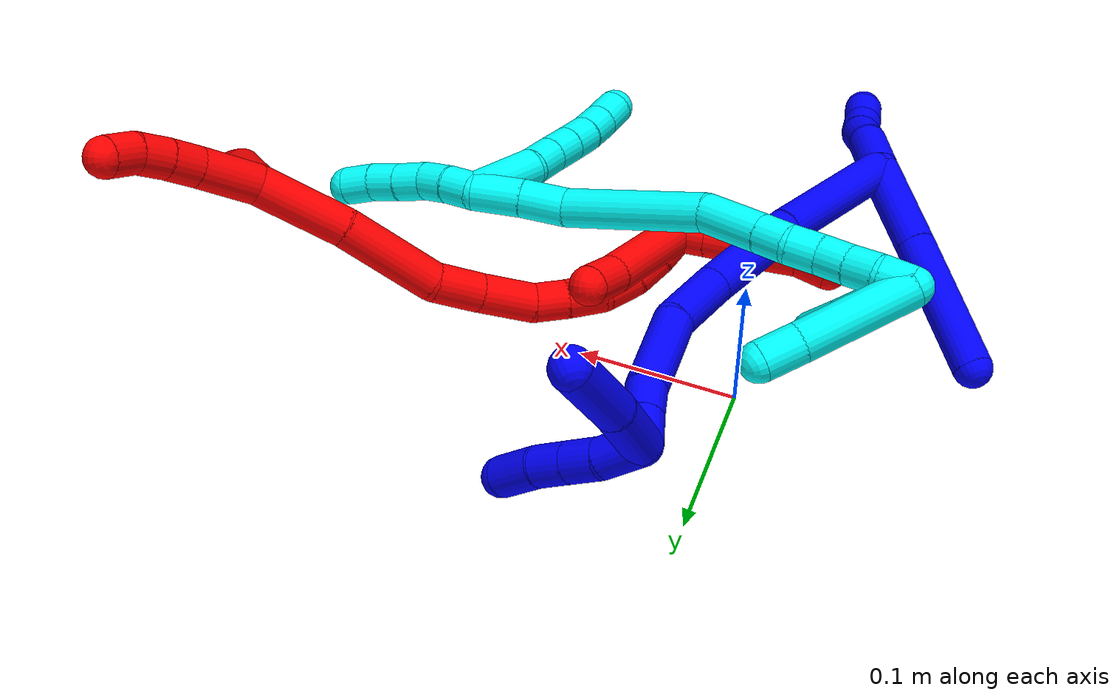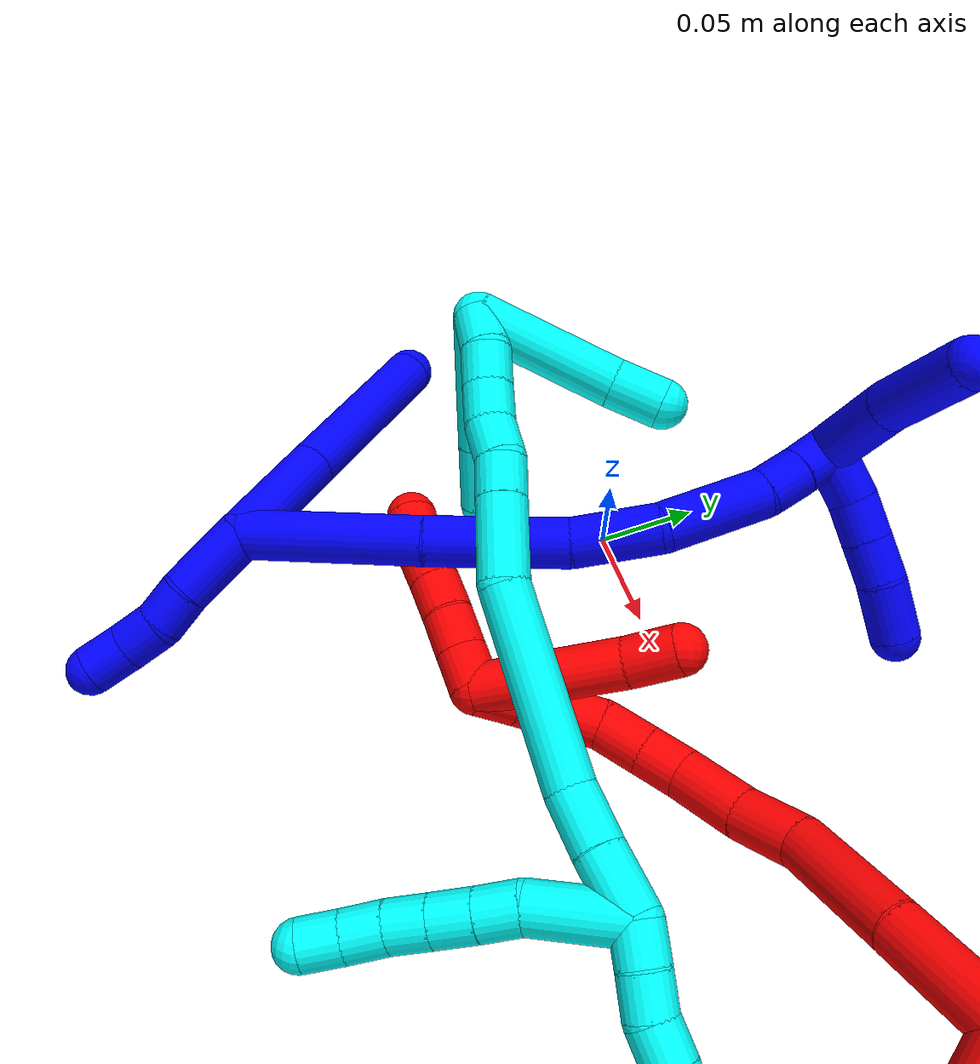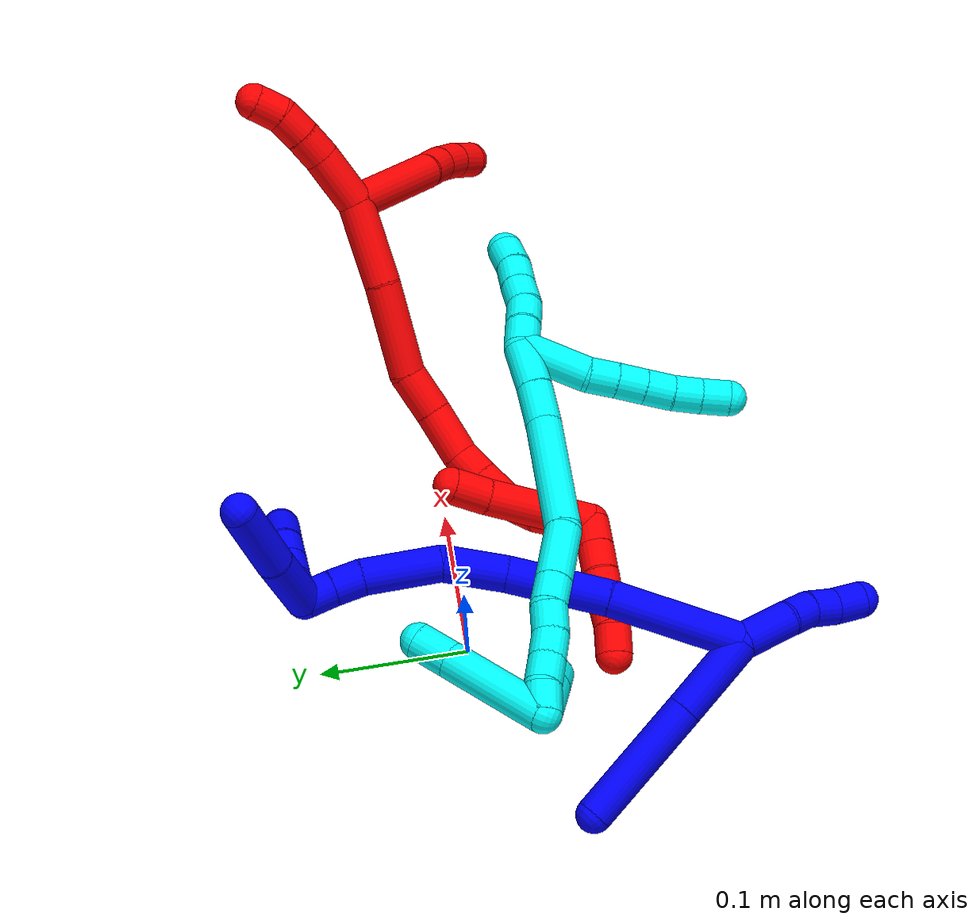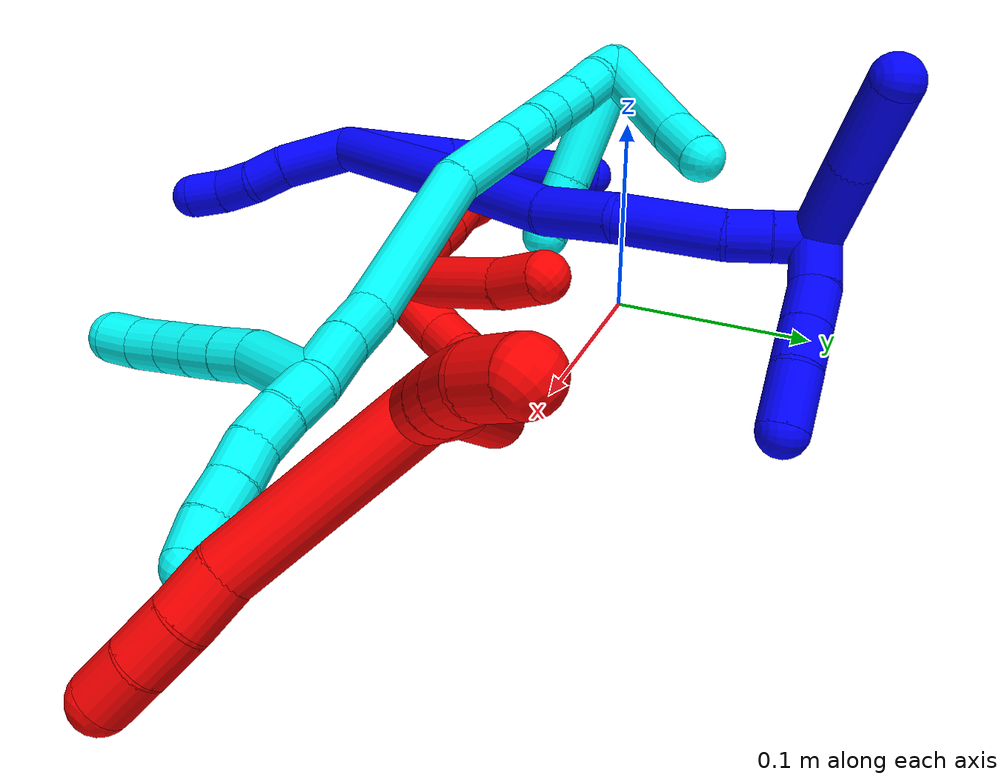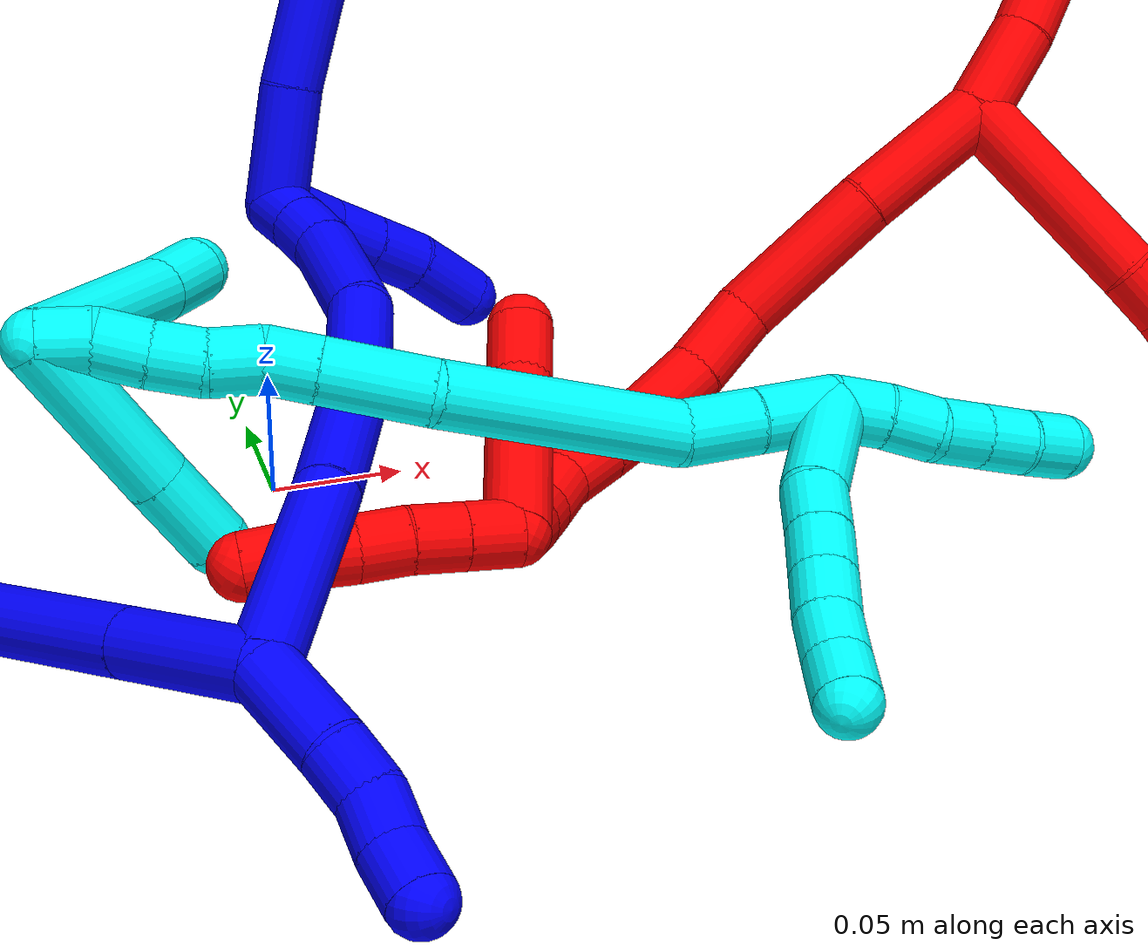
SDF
<sdf version="1.7">
 <world name="default">
  <plugin name="TubeGeneratorPlugin" filename="libtube_generator_plugin.so"/>
  <model name="photoneo_s_sensor">
   <static>1</static>
   <pose>0 0 2 1.57079 1.57079 3.14159</pose>
   <link name="link">
    <inertial><mass>0.1</mass></inertial>
    <sensor name="sensor" type="depth">
     <update_rate>30</update_rate>
     <camera>
      <horizontal_fov>1.22</horizontal_fov>
      <image><width>1920</width><height>1200</height><format>B8G8R8</format></image>
      <clip><near>0.1</near><far>4</far></clip>
      <depth_camera><output>points</output></depth_camera>
     </camera>
     <plugin name="camera_plugin" filename="libgazebo_ros_depth_camera.so">
      <baseline>0.2</baseline>
      <alwaysOn>1</alwaysOn>
      <updateRate>0.0</updateRate>
      <cameraName>camera_ir</cameraName>
      <imageTopicName>/camera/color/image_raw</imageTopicName>
      <cameraInfoTopicName>/camera/color/camera_info</cameraInfoTopicName>
      <depthImageTopicName>/camera/depth/image_raw</depthImageTopicName>
      <depthImageCameraInfoTopicName>/camera/depth/camera_info</depthImageCameraInfoTopicName>
      <pointCloudTopicName>/camera/depth/points</pointCloudTopicName>
      <frameName>fr_optical</frameName>
      <pointCloudCutoff>0.1</pointCloudCutoff>
      <pointCloudCutoffMax>2.0</pointCloudCutoffMax>
      <distortionK1>0</distortionK1>
      <distortionK2>0</distortionK2>
      <distortionK3>0</distortionK3>
      <distortionT1>0</distortionT1>
      <distortionT2>0</distortionT2>
      <CxPrime>0</CxPrime>
      <Cx>0</Cx>
      <Cy>0</Cy>
      <focalLength>0</focalLength>
      <hackBaseline>0</hackBaseline>
     </plugin>
    </sensor>
   </link>
  </model>
  <gravity>0 0 -9.8</gravity>
  <magnetic_field>6e-06 2.3e-05 -4.2e-05</magnetic_field>
  <atmosphere type="adiabatic"/>
  <physics name="default_physics" default="0" type="ode">
   <max_step_size>0.003</max_step_size>
   <real_time_factor>1</real_time_factor>
   <real_time_update_rate>1000</real_time_update_rate>
   <max_contacts>10000</max_contacts>
   <ode>
    <solver>
     <type>quick</type>
     <iters>100</iters>
     <sor>1.3</sor>
     <use_dynamic_moi_rescaling>0</use_dynamic_moi_rescaling>
    </solver>
    <constraints>
     <contact_max_correcting_vel>0</contact_max_correcting_vel>
     <contact_surface_layer>0.001</contact_surface_layer>
     <cfm>0</cfm>
     <erp>0.2</erp>
    </constraints>
   </ode>
  </physics>
  <scene><ambient>0.4 0.4 0.4 1</ambient><background>0.7 0.7 0.7 1</background><shadows>0</shadows></scene>
  <audio><device>default</device></audio>
  <spherical_coordinates>
   <surface_model>EARTH_WGS84</surface_model>
   <latitude_deg>0</latitude_deg>
   <longitude_deg>0</longitude_deg>
   <elevation>0</elevation>
   <heading_deg>0</heading_deg>
  </spherical_coordinates>
  <model name="bin">
   <static>1</static>
   <link name="bottom">
    <collision name="collision-bottom">
     <pose>0 0 -0.01 0 -0 0</pose>
     <geometry><box><size>0.8 0.6 0.02</size></box></geometry>
     <surface>
      <friction><ode><mu>100</mu><mu2>100</mu2></ode></friction>
      <contact><collide_bitmask>65535</collide_bitmask></contact>
     </surface>
    </collision>
   </link>
   <link name="west_wall">
    <collision name="collision-west_wall">
     <pose>-0.41 0 0.1 0 -0 0</pose>
     <geometry><box><size>0.02 0.6 0.2</size></box></geometry>
     <surface>
      <friction><ode><mu>100</mu><mu2>100</mu2></ode></friction>
      <contact><collide_bitmask>65535</collide_bitmask></contact>
     </surface>
    </collision>
   </link>
   <link name="east_wall">
    <collision name="collision-east_wall">
     <pose>0.41 0 0.1 0 -0 0</pose>
     <geometry><box><size>0.02 0.6 0.2</size></box></geometry>
     <surface>
      <friction><ode><mu>100</mu><mu2>100</mu2></ode></friction>
      <contact><collide_bitmask>65535</collide_bitmask></contact>
     </surface>
    </collision>
   </link>
   <link name="south_wall">
    <collision name="collision-south_wall">
     <pose>0 -0.31 0.1 0 -0 0</pose>
     <geometry><box><size>0.8 0.02 0.2</size></box></geometry>
     <surface>
      <friction><ode><mu>100</mu><mu2>100</mu2></ode></friction>
      <contact><collide_bitmask>65535</collide_bitmask></contact>
     </surface>
    </collision>
   </link>
   <link name="north_wall">
    <collision name="collision-north_wall">
     <pose>0 0.31 0.1 0 -0 0</pose>
     <geometry><box><size>0.8 0.02 0.2</size></box></geometry>
     <surface>
      <friction><ode><mu>100</mu><mu2>100</mu2></ode></friction>
      <contact><collide_bitmask>65535</collide_bitmask></contact>
     </surface>
    </collision>
   </link>
  </model>
  <model name="1">
   <static>0</static>
   <link name="1">
    <collision name="collision-cylinder-e_1_2_8">
     <pose>-0.000724 -0.001752 -0.029352 3.08196 -0.024627 -0.78309</pose>
     <geometry><cylinder><radius>0.0125</radius><length>0.058827</length></cylinder></geometry>
     <surface>
      <friction><ode><mu>1.16</mu><mu2>1.16</mu2><slip1>0</slip1><slip2>0</slip2></ode></friction>
      <contact><ode><kp>1e+06</kp><kd>1</kd><max_vel>0</max_vel><min_depth>0.001</min_depth></ode></contact>
     </surface>
    </collision>
    <visual name="visual-cylinder-e_1_2_8">
     <pose>-0.000724 -0.001752 -0.029352 3.08196 -0.024627 -0.78309</pose>
     <geometry><cylinder><radius>0.0125</radius><length>0.058827</length></cylinder></geometry>
     <material><ambient>0 0 1 1</ambient></material>
    </visual>
    <collision name="collision-cylinder-e_2_8_6">
     <pose>-0.002132 -0.006192 -0.104207 3.0826 -0.014995 -0.497709</pose>
     <geometry><cylinder><radius>0.0125</radius><length>0.091173</length></cylinder></geometry>
     <surface>
      <friction><ode><mu>1.16</mu><mu2>1.16</mu2><slip1>0</slip1><slip2>0</slip2></ode></friction>
      <contact><ode><kp>1e+06</kp><kd>1</kd><max_vel>0</max_vel><min_depth>0.001</min_depth></ode></contact>
     </surface>
    </collision>
    <visual name="visual-cylinder-e_2_8_6">
     <pose>-0.002132 -0.006192 -0.104207 3.0826 -0.014995 -0.497709</pose>
     <geometry><cylinder><radius>0.0125</radius><length>0.091173</length></cylinder></geometry>
     <material><ambient>0 0 1 1</ambient></material>
    </visual>
    <collision name="collision-cylinder-e_1_2_9">
     <pose>0.00265 -0.009238 0.016943 0.499201 0.136447 0.034833</pose>
     <geometry><cylinder><radius>0.0125</radius><length>0.038957</length></cylinder></geometry>
     <surface>
      <friction><ode><mu>1.16</mu><mu2>1.16</mu2><slip1>0</slip1><slip2>0</slip2></ode></friction>
      <contact><ode><kp>1e+06</kp><kd>1</kd><max_vel>0</max_vel><min_depth>0.001</min_depth></ode></contact>
     </surface>
    </collision>
    <visual name="visual-cylinder-e_1_2_9">
     <pose>0.00265 -0.009238 0.016943 0.499201 0.136447 0.034833</pose>
     <geometry><cylinder><radius>0.0125</radius><length>0.038957</length></cylinder></geometry>
     <material><ambient>0 0 1 1</ambient></material>
    </visual>
    <collision name="collision-cylinder-e_2_9_10">
     <pose>0.007979 -0.024075 0.041832 0.613731 0.269005 0.085706</pose>
     <geometry><cylinder><radius>0.0125</radius><length>0.020168</length></cylinder></geometry>
     <surface>
      <friction><ode><mu>1.16</mu><mu2>1.16</mu2><slip1>0</slip1><slip2>0</slip2></ode></friction>
      <contact><ode><kp>1e+06</kp><kd>1</kd><max_vel>0</max_vel><min_depth>0.001</min_depth></ode></contact>
     </surface>
    </collision>
    <visual name="visual-cylinder-e_2_9_10">
     <pose>0.007979 -0.024075 0.041832 0.613731 0.269005 0.085706</pose>
     <geometry><cylinder><radius>0.0125</radius><length>0.020168</length></cylinder></geometry>
     <material><ambient>0 0 1 1</ambient></material>
    </visual>
    <collision name="collision-cylinder-e_3_10_11">
     <pose>0.010726 -0.036708 0.056968 0.77456 0.006633 0.002706</pose>
     <geometry><cylinder><radius>0.0125</radius><length>0.020116</length></cylinder></geometry>
     <surface>
      <friction><ode><mu>1.16</mu><mu2>1.16</mu2><slip1>0</slip1><slip2>0</slip2></ode></friction>
      <contact><ode><kp>1e+06</kp><kd>1</kd><max_vel>0</max_vel><min_depth>0.001</min_depth></ode></contact>
     </surface>
    </collision>
    <visual name="visual-cylinder-e_3_10_11">
     <pose>0.010726 -0.036708 0.056968 0.77456 0.006633 0.002706</pose>
     <geometry><cylinder><radius>0.0125</radius><length>0.020116</length></cylinder></geometry>
     <material><ambient>0 0 1 1</ambient></material>
    </visual>
    <collision name="collision-cylinder-e_4_11_5">
     <pose>0.010227 -0.049651 0.072672 0.6066 -0.054572 -0.017083</pose>
     <geometry><cylinder><radius>0.0125</radius><length>0.020759</length></cylinder></geometry>
     <surface>
      <friction><ode><mu>1.16</mu><mu2>1.16</mu2><slip1>0</slip1><slip2>0</slip2></ode></friction>
      <contact><ode><kp>1e+06</kp><kd>1</kd><max_vel>0</max_vel><min_depth>0.001</min_depth></ode></contact>
     </surface>
    </collision>
    <visual name="visual-cylinder-e_4_11_5">
     <pose>0.010227 -0.049651 0.072672 0.6066 -0.054572 -0.017083</pose>
     <geometry><cylinder><radius>0.0125</radius><length>0.020759</length></cylinder></geometry>
     <material><ambient>0 0 1 1</ambient></material>
    </visual>
    <collision name="collision-cylinder-e_1_2_12">
     <pose>0.025167 0.032637 -0.019979 -2.12011 0.581748 -0.981359</pose>
     <geometry><cylinder><radius>0.0125</radius><length>0.091602</length></cylinder></geometry>
     <surface>
      <friction><ode><mu>1.16</mu><mu2>1.16</mu2><slip1>0</slip1><slip2>0</slip2></ode></friction>
      <contact><ode><kp>1e+06</kp><kd>1</kd><max_vel>0</max_vel><min_depth>0.001</min_depth></ode></contact>
     </surface>
    </collision>
    <visual name="visual-cylinder-e_1_2_12">
     <pose>0.025167 0.032637 -0.019979 -2.12011 0.581748 -0.981359</pose>
     <geometry><cylinder><radius>0.0125</radius><length>0.091602</length></cylinder></geometry>
     <material><ambient>0 0 1 1</ambient></material>
    </visual>
    <collision name="collision-cylinder-e_2_12_13">
     <pose>0.070073 0.088241 -0.057796 -2.23114 0.596349 -1.12128</pose>
     <geometry><cylinder><radius>0.0125</radius><length>0.070292</length></cylinder></geometry>
     <surface>
      <friction><ode><mu>1.16</mu><mu2>1.16</mu2><slip1>0</slip1><slip2>0</slip2></ode></friction>
      <contact><ode><kp>1e+06</kp><kd>1</kd><max_vel>0</max_vel><min_depth>0.001</min_depth></ode></contact>
     </surface>
    </collision>
    <visual name="visual-cylinder-e_2_12_13">
     <pose>0.070073 0.088241 -0.057796 -2.23114 0.596349 -1.12128</pose>
     <geometry><cylinder><radius>0.0125</radius><length>0.070292</length></cylinder></geometry>
     <material><ambient>0 0 1 1</ambient></material>
    </visual>
    <collision name="collision-cylinder-e_3_13_14">
     <pose>0.098523 0.126734 -0.08812 -2.24811 0.412175 -0.822983</pose>
     <geometry><cylinder><radius>0.0125</radius><length>0.043491</length></cylinder></geometry>
     <surface>
      <friction><ode><mu>1.16</mu><mu2>1.16</mu2><slip1>0</slip1><slip2>0</slip2></ode></friction>
      <contact><ode><kp>1e+06</kp><kd>1</kd><max_vel>0</max_vel><min_depth>0.001</min_depth></ode></contact>
     </surface>
    </collision>
    <visual name="visual-cylinder-e_3_13_14">
     <pose>0.098523 0.126734 -0.08812 -2.24811 0.412175 -0.822983</pose>
     <geometry><cylinder><radius>0.0125</radius><length>0.043491</length></cylinder></geometry>
     <material><ambient>0 0 1 1</ambient></material>
    </visual>
    <collision name="collision-cylinder-e_4_14_15">
     <pose>0.116143 0.1551 -0.122303 -2.60724 0.339654 -1.11931</pose>
     <geometry><cylinder><radius>0.0125</radius><length>0.053479</length></cylinder></geometry>
     <surface>
      <friction><ode><mu>1.16</mu><mu2>1.16</mu2><slip1>0</slip1><slip2>0</slip2></ode></friction>
      <contact><ode><kp>1e+06</kp><kd>1</kd><max_vel>0</max_vel><min_depth>0.001</min_depth></ode></contact>
     </surface>
    </collision>
    <visual name="visual-cylinder-e_4_14_15">
     <pose>0.116143 0.1551 -0.122303 -2.60724 0.339654 -1.11931</pose>
     <geometry><cylinder><radius>0.0125</radius><length>0.053479</length></cylinder></geometry>
     <material><ambient>0 0 1 1</ambient></material>
    </visual>
    <collision name="collision-cylinder-e_5_15_16">
     <pose>0.126665 0.17223 -0.153511 -2.71786 0.153444 -0.686488</pose>
     <geometry><cylinder><radius>0.0125</radius><length>0.021114</length></cylinder></geometry>
     <surface>
      <friction><ode><mu>1.16</mu><mu2>1.16</mu2><slip1>0</slip1><slip2>0</slip2></ode></friction>
      <contact><ode><kp>1e+06</kp><kd>1</kd><max_vel>0</max_vel><min_depth>0.001</min_depth></ode></contact>
     </surface>
    </collision>
    <visual name="visual-cylinder-e_5_15_16">
     <pose>0.126665 0.17223 -0.153511 -2.71786 0.153444 -0.686488</pose>
     <geometry><cylinder><radius>0.0125</radius><length>0.021114</length></cylinder></geometry>
     <material><ambient>0 0 1 1</ambient></material>
    </visual>
    <collision name="collision-cylinder-e_6_16_1">
     <pose>0.129422 0.180156 -0.172277 -2.76722 0.114432 -0.587342</pose>
     <geometry><cylinder><radius>0.0125</radius><length>0.020022</length></cylinder></geometry>
     <surface>
      <friction><ode><mu>1.16</mu><mu2>1.16</mu2><slip1>0</slip1><slip2>0</slip2></ode></friction>
      <contact><ode><kp>1e+06</kp><kd>1</kd><max_vel>0</max_vel><min_depth>0.001</min_depth></ode></contact>
     </surface>
    </collision>
    <visual name="visual-cylinder-e_6_16_1">
     <pose>0.129422 0.180156 -0.172277 -2.76722 0.114432 -0.587342</pose>
     <geometry><cylinder><radius>0.0125</radius><length>0.020022</length></cylinder></geometry>
     <material><ambient>0 0 1 1</ambient></material>
    </visual>
    <collision name="collision-cylinder-e_1_1_17">
     <pose>0.123494 0.206609 -0.180233 -1.51386 -0.30008 0.28369</pose>
     <geometry><cylinder><radius>0.0125</radius><length>0.047843</length></cylinder></geometry>
     <surface>
      <friction><ode><mu>1.16</mu><mu2>1.16</mu2><slip1>0</slip1><slip2>0</slip2></ode></friction>
      <contact><ode><kp>1e+06</kp><kd>1</kd><max_vel>0</max_vel><min_depth>0.001</min_depth></ode></contact>
     </surface>
    </collision>
    <visual name="visual-cylinder-e_1_1_17">
     <pose>0.123494 0.206609 -0.180233 -1.51386 -0.30008 0.28369</pose>
     <geometry><cylinder><radius>0.0125</radius><length>0.047843</length></cylinder></geometry>
     <material><ambient>0 0 1 1</ambient></material>
    </visual>
    <collision name="collision-cylinder-e_2_17_4">
     <pose>0.11127 0.254826 -0.176055 -1.45799 -0.198886 0.177745</pose>
     <geometry><cylinder><radius>0.0125</radius><length>0.052157</length></cylinder></geometry>
     <surface>
      <friction><ode><mu>1.16</mu><mu2>1.16</mu2><slip1>0</slip1><slip2>0</slip2></ode></friction>
      <contact><ode><kp>1e+06</kp><kd>1</kd><max_vel>0</max_vel><min_depth>0.001</min_depth></ode></contact>
     </surface>
    </collision>
    <visual name="visual-cylinder-e_2_17_4">
     <pose>0.11127 0.254826 -0.176055 -1.45799 -0.198886 0.177745</pose>
     <geometry><cylinder><radius>0.0125</radius><length>0.052157</length></cylinder></geometry>
     <material><ambient>0 0 1 1</ambient></material>
    </visual>
    <collision name="collision-cylinder-e_1_1_18">
     <pose>0.143857 0.184051 -0.17926 -0.113062 1.40028 -0.095287</pose>
     <geometry><cylinder><radius>0.0125</radius><length>0.026976</length></cylinder></geometry>
     <surface>
      <friction><ode><mu>1.16</mu><mu2>1.16</mu2><slip1>0</slip1><slip2>0</slip2></ode></friction>
      <contact><ode><kp>1e+06</kp><kd>1</kd><max_vel>0</max_vel><min_depth>0.001</min_depth></ode></contact>
     </surface>
    </collision>
    <visual name="visual-cylinder-e_1_1_18">
     <pose>0.143857 0.184051 -0.17926 -0.113062 1.40028 -0.095287</pose>
     <geometry><cylinder><radius>0.0125</radius><length>0.026976</length></cylinder></geometry>
     <material><ambient>0 0 1 1</ambient></material>
    </visual>
    <collision name="collision-cylinder-e_2_18_19">
     <pose>0.167219 0.18431 -0.173236 2.8e-05 1.21429 2e-05</pose>
     <geometry><cylinder><radius>0.0125</radius><length>0.021489</length></cylinder></geometry>
     <surface>
      <friction><ode><mu>1.16</mu><mu2>1.16</mu2><slip1>0</slip1><slip2>0</slip2></ode></friction>
      <contact><ode><kp>1e+06</kp><kd>1</kd><max_vel>0</max_vel><min_depth>0.001</min_depth></ode></contact>
     </surface>
    </collision>
    <visual name="visual-cylinder-e_2_18_19">
     <pose>0.167219 0.18431 -0.173236 2.8e-05 1.21429 2e-05</pose>
     <geometry><cylinder><radius>0.0125</radius><length>0.021489</length></cylinder></geometry>
     <material><ambient>0 0 1 1</ambient></material>
    </visual>
    <collision name="collision-cylinder-e_3_19_20">
     <pose>0.187546 0.184299 -0.16571 0.002816 1.2181 0.001964</pose>
     <geometry><cylinder><radius>0.0125</radius><length>0.021862</length></cylinder></geometry>
     <surface>
      <friction><ode><mu>1.16</mu><mu2>1.16</mu2><slip1>0</slip1><slip2>0</slip2></ode></friction>
      <contact><ode><kp>1e+06</kp><kd>1</kd><max_vel>0</max_vel><min_depth>0.001</min_depth></ode></contact>
     </surface>
    </collision>
    <visual name="visual-cylinder-e_3_19_20">
     <pose>0.187546 0.184299 -0.16571 0.002816 1.2181 0.001964</pose>
     <geometry><cylinder><radius>0.0125</radius><length>0.021862</length></cylinder></geometry>
     <material><ambient>0 0 1 1</ambient></material>
    </visual>
    <collision name="collision-cylinder-e_4_20_3">
     <pose>0.211837 0.181894 -0.157754 0.520137 1.24012 0.375508</pose>
     <geometry><cylinder><radius>0.0125</radius><length>0.029673</length></cylinder></geometry>
     <surface>
      <friction><ode><mu>1.16</mu><mu2>1.16</mu2><slip1>0</slip1><slip2>0</slip2></ode></friction>
      <contact><ode><kp>1e+06</kp><kd>1</kd><max_vel>0</max_vel><min_depth>0.001</min_depth></ode></contact>
     </surface>
    </collision>
    <visual name="visual-cylinder-e_4_20_3">
     <pose>0.211837 0.181894 -0.157754 0.520137 1.24012 0.375508</pose>
     <geometry><cylinder><radius>0.0125</radius><length>0.029673</length></cylinder></geometry>
     <material><ambient>0 0 1 1</ambient></material>
    </visual>
    <collision name="collision-sphere-3">
     <pose>0.225869 0.1795 -0.153574 0 -0 0</pose>
     <geometry><sphere><radius>0.0125</radius></sphere></geometry>
     <surface>
      <friction><ode><mu>1.16</mu><mu2>1.16</mu2><slip1>0</slip1><slip2>0</slip2></ode></friction>
      <contact><ode><kp>1e+06</kp><kd>1</kd><max_vel>0</max_vel><min_depth>0.001</min_depth></ode></contact>
     </surface>
    </collision>
    <visual name="visual-sphere-3">
     <pose>0.225869 0.1795 -0.153574 0 -0 0</pose>
     <geometry><sphere><radius>0.0125</radius></sphere></geometry>
     <material><ambient>0 0 1 1</ambient></material>
    </visual>
    <collision name="collision-sphere-20">
     <pose>0.197804 0.184288 -0.161934 0 -0 0</pose>
     <geometry><sphere><radius>0.0125</radius></sphere></geometry>
     <surface>
      <friction><ode><mu>1.16</mu><mu2>1.16</mu2><slip1>0</slip1><slip2>0</slip2></ode></friction>
      <contact><ode><kp>1e+06</kp><kd>1</kd><max_vel>0</max_vel><min_depth>0.001</min_depth></ode></contact>
     </surface>
    </collision>
    <visual name="visual-sphere-20">
     <pose>0.197804 0.184288 -0.161934 0 -0 0</pose>
     <geometry><sphere><radius>0.0125</radius></sphere></geometry>
     <material><ambient>0 0 1 1</ambient></material>
    </visual>
    <collision name="collision-sphere-19">
     <pose>0.177287 0.184309 -0.169486 0 -0 0</pose>
     <geometry><sphere><radius>0.0125</radius></sphere></geometry>
     <surface>
      <friction><ode><mu>1.16</mu><mu2>1.16</mu2><slip1>0</slip1><slip2>0</slip2></ode></friction>
      <contact><ode><kp>1e+06</kp><kd>1</kd><max_vel>0</max_vel><min_depth>0.001</min_depth></ode></contact>
     </surface>
    </collision>
    <visual name="visual-sphere-19">
     <pose>0.177287 0.184309 -0.169486 0 -0 0</pose>
     <geometry><sphere><radius>0.0125</radius></sphere></geometry>
     <material><ambient>0 0 1 1</ambient></material>
    </visual>
    <collision name="collision-sphere-11">
     <pose>0.010793 -0.043743 0.064157 0 -0 0</pose>
     <geometry><sphere><radius>0.0125</radius></sphere></geometry>
     <surface>
      <friction><ode><mu>1.16</mu><mu2>1.16</mu2><slip1>0</slip1><slip2>0</slip2></ode></friction>
      <contact><ode><kp>1e+06</kp><kd>1</kd><max_vel>0</max_vel><min_depth>0.001</min_depth></ode></contact>
     </surface>
    </collision>
    <visual name="visual-sphere-11">
     <pose>0.010793 -0.043743 0.064157 0 -0 0</pose>
     <geometry><sphere><radius>0.0125</radius></sphere></geometry>
     <material><ambient>0 0 1 1</ambient></material>
    </visual>
    <collision name="collision-sphere-10">
     <pose>0.010659 -0.029674 0.04978 0 -0 0</pose>
     <geometry><sphere><radius>0.0125</radius></sphere></geometry>
     <surface>
      <friction><ode><mu>1.16</mu><mu2>1.16</mu2><slip1>0</slip1><slip2>0</slip2></ode></friction>
      <contact><ode><kp>1e+06</kp><kd>1</kd><max_vel>0</max_vel><min_depth>0.001</min_depth></ode></contact>
     </surface>
    </collision>
    <visual name="visual-sphere-10">
     <pose>0.010659 -0.029674 0.04978 0 -0 0</pose>
     <geometry><sphere><radius>0.0125</radius></sphere></geometry>
     <material><ambient>0 0 1 1</ambient></material>
    </visual>
    <collision name="collision-sphere-6">
     <pose>-0.002816 -0.00888 -0.149709 0 -0 0</pose>
     <geometry><sphere><radius>0.0125</radius></sphere></geometry>
     <surface>
      <friction><ode><mu>1.16</mu><mu2>1.16</mu2><slip1>0</slip1><slip2>0</slip2></ode></friction>
      <contact><ode><kp>1e+06</kp><kd>1</kd><max_vel>0</max_vel><min_depth>0.001</min_depth></ode></contact>
     </surface>
    </collision>
    <visual name="visual-sphere-6">
     <pose>-0.002816 -0.00888 -0.149709 0 -0 0</pose>
     <geometry><sphere><radius>0.0125</radius></sphere></geometry>
     <material><ambient>0 0 1 1</ambient></material>
    </visual>
    <collision name="collision-sphere-9">
     <pose>0.005299 -0.018476 0.033885 0 -0 0</pose>
     <geometry><sphere><radius>0.0125</radius></sphere></geometry>
     <surface>
      <friction><ode><mu>1.16</mu><mu2>1.16</mu2><slip1>0</slip1><slip2>0</slip2></ode></friction>
      <contact><ode><kp>1e+06</kp><kd>1</kd><max_vel>0</max_vel><min_depth>0.001</min_depth></ode></contact>
     </surface>
    </collision>
    <visual name="visual-sphere-9">
     <pose>0.005299 -0.018476 0.033885 0 -0 0</pose>
     <geometry><sphere><radius>0.0125</radius></sphere></geometry>
     <material><ambient>0 0 1 1</ambient></material>
    </visual>
    <collision name="collision-sphere-2">
     <geometry><sphere><radius>0.0125</radius></sphere></geometry>
     <surface>
      <friction><ode><mu>1.16</mu><mu2>1.16</mu2><slip1>0</slip1><slip2>0</slip2></ode></friction>
      <contact><ode><kp>1e+06</kp><kd>1</kd><max_vel>0</max_vel><min_depth>0.001</min_depth></ode></contact>
     </surface>
    </collision>
    <visual name="visual-sphere-2">
     <geometry><sphere><radius>0.0125</radius></sphere></geometry>
     <material><ambient>0 0 1 1</ambient></material>
    </visual>
    <collision name="collision-sphere-8">
     <pose>-0.001449 -0.003505 -0.058705 0 -0 0</pose>
     <geometry><sphere><radius>0.0125</radius></sphere></geometry>
     <surface>
      <friction><ode><mu>1.16</mu><mu2>1.16</mu2><slip1>0</slip1><slip2>0</slip2></ode></friction>
      <contact><ode><kp>1e+06</kp><kd>1</kd><max_vel>0</max_vel><min_depth>0.001</min_depth></ode></contact>
     </surface>
    </collision>
    <visual name="visual-sphere-8">
     <pose>-0.001449 -0.003505 -0.058705 0 -0 0</pose>
     <geometry><sphere><radius>0.0125</radius></sphere></geometry>
     <material><ambient>0 0 1 1</ambient></material>
    </visual>
    <collision name="collision-sphere-5">
     <pose>0.00966 -0.055559 0.081187 0 -0 0</pose>
     <geometry><sphere><radius>0.0125</radius></sphere></geometry>
     <surface>
      <friction><ode><mu>1.16</mu><mu2>1.16</mu2><slip1>0</slip1><slip2>0</slip2></ode></friction>
      <contact><ode><kp>1e+06</kp><kd>1</kd><max_vel>0</max_vel><min_depth>0.001</min_depth></ode></contact>
     </surface>
    </collision>
    <visual name="visual-sphere-5">
     <pose>0.00966 -0.055559 0.081187 0 -0 0</pose>
     <geometry><sphere><radius>0.0125</radius></sphere></geometry>
     <material><ambient>0 0 1 1</ambient></material>
    </visual>
    <collision name="collision-sphere-12">
     <pose>0.050334 0.065275 -0.039958 0 -0 0</pose>
     <geometry><sphere><radius>0.0125</radius></sphere></geometry>
     <surface>
      <friction><ode><mu>1.16</mu><mu2>1.16</mu2><slip1>0</slip1><slip2>0</slip2></ode></friction>
      <contact><ode><kp>1e+06</kp><kd>1</kd><max_vel>0</max_vel><min_depth>0.001</min_depth></ode></contact>
     </surface>
    </collision>
    <visual name="visual-sphere-12">
     <pose>0.050334 0.065275 -0.039958 0 -0 0</pose>
     <geometry><sphere><radius>0.0125</radius></sphere></geometry>
     <material><ambient>0 0 1 1</ambient></material>
    </visual>
    <collision name="collision-sphere-13">
     <pose>0.089812 0.111208 -0.075633 0 -0 0</pose>
     <geometry><sphere><radius>0.0125</radius></sphere></geometry>
     <surface>
      <friction><ode><mu>1.16</mu><mu2>1.16</mu2><slip1>0</slip1><slip2>0</slip2></ode></friction>
      <contact><ode><kp>1e+06</kp><kd>1</kd><max_vel>0</max_vel><min_depth>0.001</min_depth></ode></contact>
     </surface>
    </collision>
    <visual name="visual-sphere-13">
     <pose>0.089812 0.111208 -0.075633 0 -0 0</pose>
     <geometry><sphere><radius>0.0125</radius></sphere></geometry>
     <material><ambient>0 0 1 1</ambient></material>
    </visual>
    <collision name="collision-sphere-14">
     <pose>0.107235 0.14226 -0.100606 0 -0 0</pose>
     <geometry><sphere><radius>0.0125</radius></sphere></geometry>
     <surface>
      <friction><ode><mu>1.16</mu><mu2>1.16</mu2><slip1>0</slip1><slip2>0</slip2></ode></friction>
      <contact><ode><kp>1e+06</kp><kd>1</kd><max_vel>0</max_vel><min_depth>0.001</min_depth></ode></contact>
     </surface>
    </collision>
    <visual name="visual-sphere-14">
     <pose>0.107235 0.14226 -0.100606 0 -0 0</pose>
     <geometry><sphere><radius>0.0125</radius></sphere></geometry>
     <material><ambient>0 0 1 1</ambient></material>
    </visual>
    <collision name="collision-sphere-15">
     <pose>0.125052 0.16794 -0.144001 0 -0 0</pose>
     <geometry><sphere><radius>0.0125</radius></sphere></geometry>
     <surface>
      <friction><ode><mu>1.16</mu><mu2>1.16</mu2><slip1>0</slip1><slip2>0</slip2></ode></friction>
      <contact><ode><kp>1e+06</kp><kd>1</kd><max_vel>0</max_vel><min_depth>0.001</min_depth></ode></contact>
     </surface>
    </collision>
    <visual name="visual-sphere-15">
     <pose>0.125052 0.16794 -0.144001 0 -0 0</pose>
     <geometry><sphere><radius>0.0125</radius></sphere></geometry>
     <material><ambient>0 0 1 1</ambient></material>
    </visual>
    <collision name="collision-sphere-16">
     <pose>0.128279 0.176519 -0.163021 0 -0 0</pose>
     <geometry><sphere><radius>0.0125</radius></sphere></geometry>
     <surface>
      <friction><ode><mu>1.16</mu><mu2>1.16</mu2><slip1>0</slip1><slip2>0</slip2></ode></friction>
      <contact><ode><kp>1e+06</kp><kd>1</kd><max_vel>0</max_vel><min_depth>0.001</min_depth></ode></contact>
     </surface>
    </collision>
    <visual name="visual-sphere-16">
     <pose>0.128279 0.176519 -0.163021 0 -0 0</pose>
     <geometry><sphere><radius>0.0125</radius></sphere></geometry>
     <material><ambient>0 0 1 1</ambient></material>
    </visual>
    <collision name="collision-sphere-1">
     <pose>0.130565 0.183793 -0.181534 0 -0 0</pose>
     <geometry><sphere><radius>0.0125</radius></sphere></geometry>
     <surface>
      <friction><ode><mu>1.16</mu><mu2>1.16</mu2><slip1>0</slip1><slip2>0</slip2></ode></friction>
      <contact><ode><kp>1e+06</kp><kd>1</kd><max_vel>0</max_vel><min_depth>0.001</min_depth></ode></contact>
     </surface>
    </collision>
    <visual name="visual-sphere-1">
     <pose>0.130565 0.183793 -0.181534 0 -0 0</pose>
     <geometry><sphere><radius>0.0125</radius></sphere></geometry>
     <material><ambient>0 0 1 1</ambient></material>
    </visual>
    <collision name="collision-sphere-18">
     <pose>0.15715 0.18431 -0.176986 0 -0 0</pose>
     <geometry><sphere><radius>0.0125</radius></sphere></geometry>
     <surface>
      <friction><ode><mu>1.16</mu><mu2>1.16</mu2><slip1>0</slip1><slip2>0</slip2></ode></friction>
      <contact><ode><kp>1e+06</kp><kd>1</kd><max_vel>0</max_vel><min_depth>0.001</min_depth></ode></contact>
     </surface>
    </collision>
    <visual name="visual-sphere-18">
     <pose>0.15715 0.18431 -0.176986 0 -0 0</pose>
     <geometry><sphere><radius>0.0125</radius></sphere></geometry>
     <material><ambient>0 0 1 1</ambient></material>
    </visual>
    <collision name="collision-sphere-17">
     <pose>0.116423 0.229424 -0.178933 0 -0 0</pose>
     <geometry><sphere><radius>0.0125</radius></sphere></geometry>
     <surface>
      <friction><ode><mu>1.16</mu><mu2>1.16</mu2><slip1>0</slip1><slip2>0</slip2></ode></friction>
      <contact><ode><kp>1e+06</kp><kd>1</kd><max_vel>0</max_vel><min_depth>0.001</min_depth></ode></contact>
     </surface>
    </collision>
    <visual name="visual-sphere-17">
     <pose>0.116423 0.229424 -0.178933 0 -0 0</pose>
     <geometry><sphere><radius>0.0125</radius></sphere></geometry>
     <material><ambient>0 0 1 1</ambient></material>
    </visual>
    <collision name="collision-sphere-4">
     <pose>0.106118 0.280228 -0.173177 0 -0 0</pose>
     <geometry><sphere><radius>0.0125</radius></sphere></geometry>
     <surface>
      <friction><ode><mu>1.16</mu><mu2>1.16</mu2><slip1>0</slip1><slip2>0</slip2></ode></friction>
      <contact><ode><kp>1e+06</kp><kd>1</kd><max_vel>0</max_vel><min_depth>0.001</min_depth></ode></contact>
     </surface>
    </collision>
    <visual name="visual-sphere-4">
     <pose>0.106118 0.280228 -0.173177 0 -0 0</pose>
     <geometry><sphere><radius>0.0125</radius></sphere></geometry>
     <material><ambient>0 0 1 1</ambient></material>
    </visual>
    <inertial>
     <pose>0.070693 0.091317 -0.086258 0 -0 0</pose>
     <mass>0.75</mass>
     <inertia>
      <ixx>5.2e-05</ixx>
      <ixy>0</ixy>
      <ixz>0</ixz>
      <iyy>-0.00016</iyy>
      <iyz>0</iyz>
      <izz>-0.000179</izz>
     </inertia>
    </inertial>
   </link>
   <pose>-0.040324 -0.178057 0.044527 1.32925 0.672241 0.468318</pose>
  </model>
  <model name="2">
   <static>0</static>
   <link name="2">
    <collision name="collision-cylinder-e_1_2_8">
     <pose>-0.018029 0.002023 0.039115 -0.051672 -0.431383 0.011324</pose>
     <geometry><cylinder><radius>0.0125</radius><length>0.086235</length></cylinder></geometry>
     <surface>
      <friction><ode><mu>1.16</mu><mu2>1.16</mu2><slip1>0</slip1><slip2>0</slip2></ode></friction>
      <contact><ode><kp>1e+06</kp><kd>1</kd><max_vel>0</max_vel><min_depth>0.001</min_depth></ode></contact>
     </surface>
    </collision>
    <visual name="visual-cylinder-e_1_2_8">
     <pose>-0.018029 0.002023 0.039115 -0.051672 -0.431383 0.011324</pose>
     <geometry><cylinder><radius>0.0125</radius><length>0.086235</length></cylinder></geometry>
     <material><ambient>1 0 0 1</ambient></material>
    </visual>
    <collision name="collision-cylinder-e_2_8_9">
     <pose>-0.039819 0.002986 0.088537 0.102471 -0.348289 -0.018043</pose>
     <geometry><cylinder><radius>0.0125</radius><length>0.022044</length></cylinder></geometry>
     <surface>
      <friction><ode><mu>1.16</mu><mu2>1.16</mu2><slip1>0</slip1><slip2>0</slip2></ode></friction>
      <contact><ode><kp>1e+06</kp><kd>1</kd><max_vel>0</max_vel><min_depth>0.001</min_depth></ode></contact>
     </surface>
    </collision>
    <visual name="visual-cylinder-e_2_8_9">
     <pose>-0.039819 0.002986 0.088537 0.102471 -0.348289 -0.018043</pose>
     <geometry><cylinder><radius>0.0125</radius><length>0.022044</length></cylinder></geometry>
     <material><ambient>1 0 0 1</ambient></material>
    </visual>
    <collision name="collision-cylinder-e_3_9_10">
     <pose>-0.04857 0.001187 0.108145 0.079337 -0.491 -0.019888</pose>
     <geometry><cylinder><radius>0.0125</radius><length>0.021164</length></cylinder></geometry>
     <surface>
      <friction><ode><mu>1.16</mu><mu2>1.16</mu2><slip1>0</slip1><slip2>0</slip2></ode></friction>
      <contact><ode><kp>1e+06</kp><kd>1</kd><max_vel>0</max_vel><min_depth>0.001</min_depth></ode></contact>
     </surface>
    </collision>
    <visual name="visual-cylinder-e_3_9_10">
     <pose>-0.04857 0.001187 0.108145 0.079337 -0.491 -0.019888</pose>
     <geometry><cylinder><radius>0.0125</radius><length>0.021164</length></cylinder></geometry>
     <material><ambient>1 0 0 1</ambient></material>
    </visual>
    <collision name="collision-cylinder-e_4_10_6">
     <pose>-0.059433 -0.000559 0.125823 0.119575 -0.608187 -0.037566</pose>
     <geometry><cylinder><radius>0.0125</radius><length>0.020556</length></cylinder></geometry>
     <surface>
      <friction><ode><mu>1.16</mu><mu2>1.16</mu2><slip1>0</slip1><slip2>0</slip2></ode></friction>
      <contact><ode><kp>1e+06</kp><kd>1</kd><max_vel>0</max_vel><min_depth>0.001</min_depth></ode></contact>
     </surface>
    </collision>
    <visual name="visual-cylinder-e_4_10_6">
     <pose>-0.059433 -0.000559 0.125823 0.119575 -0.608187 -0.037566</pose>
     <geometry><cylinder><radius>0.0125</radius><length>0.020556</length></cylinder></geometry>
     <material><ambient>1 0 0 1</ambient></material>
    </visual>
    <collision name="collision-cylinder-e_1_2_11">
     <pose>0.018888 0.004623 0.002366 -1.09771 1.30249 -0.872307</pose>
     <geometry><cylinder><radius>0.0125</radius><length>0.039178</length></cylinder></geometry>
     <surface>
      <friction><ode><mu>1.16</mu><mu2>1.16</mu2><slip1>0</slip1><slip2>0</slip2></ode></friction>
      <contact><ode><kp>1e+06</kp><kd>1</kd><max_vel>0</max_vel><min_depth>0.001</min_depth></ode></contact>
     </surface>
    </collision>
    <visual name="visual-cylinder-e_1_2_11">
     <pose>0.018888 0.004623 0.002366 -1.09771 1.30249 -0.872307</pose>
     <geometry><cylinder><radius>0.0125</radius><length>0.039178</length></cylinder></geometry>
     <material><ambient>1 0 0 1</ambient></material>
    </visual>
    <collision name="collision-cylinder-e_2_11_12">
     <pose>0.047673 0.011321 0.004861 -1.5089 1.3637 -1.30351</pose>
     <geometry><cylinder><radius>0.0125</radius><length>0.020224</length></cylinder></geometry>
     <surface>
      <friction><ode><mu>1.16</mu><mu2>1.16</mu2><slip1>0</slip1><slip2>0</slip2></ode></friction>
      <contact><ode><kp>1e+06</kp><kd>1</kd><max_vel>0</max_vel><min_depth>0.001</min_depth></ode></contact>
     </surface>
    </collision>
    <visual name="visual-cylinder-e_2_11_12">
     <pose>0.047673 0.011321 0.004861 -1.5089 1.3637 -1.30351</pose>
     <geometry><cylinder><radius>0.0125</radius><length>0.020224</length></cylinder></geometry>
     <material><ambient>1 0 0 1</ambient></material>
    </visual>
    <collision name="collision-cylinder-e_3_12_13">
     <pose>0.06758 0.01484 0.004973 -1.58252 1.42754 -1.43915</pose>
     <geometry><cylinder><radius>0.0125</radius><length>0.020229</length></cylinder></geometry>
     <surface>
      <friction><ode><mu>1.16</mu><mu2>1.16</mu2><slip1>0</slip1><slip2>0</slip2></ode></friction>
      <contact><ode><kp>1e+06</kp><kd>1</kd><max_vel>0</max_vel><min_depth>0.001</min_depth></ode></contact>
     </surface>
    </collision>
    <visual name="visual-cylinder-e_3_12_13">
     <pose>0.06758 0.01484 0.004973 -1.58252 1.42754 -1.43915</pose>
     <geometry><cylinder><radius>0.0125</radius><length>0.020229</length></cylinder></geometry>
     <material><ambient>1 0 0 1</ambient></material>
    </visual>
    <collision name="collision-cylinder-e_4_13_5">
     <pose>0.087545 0.014951 0.003264 2.47436 1.35767 2.33008</pose>
     <geometry><cylinder><radius>0.0125</radius><length>0.020368</length></cylinder></geometry>
     <surface>
      <friction><ode><mu>1.16</mu><mu2>1.16</mu2><slip1>0</slip1><slip2>0</slip2></ode></friction>
      <contact><ode><kp>1e+06</kp><kd>1</kd><max_vel>0</max_vel><min_depth>0.001</min_depth></ode></contact>
     </surface>
    </collision>
    <visual name="visual-cylinder-e_4_13_5">
     <pose>0.087545 0.014951 0.003264 2.47436 1.35767 2.33008</pose>
     <geometry><cylinder><radius>0.0125</radius><length>0.020368</length></cylinder></geometry>
     <material><ambient>1 0 0 1</ambient></material>
    </visual>
    <collision name="collision-cylinder-e_1_2_14">
     <pose>-0.023688 -0.01153 -0.012164 2.38296 -0.955035 -1.82881</pose>
     <geometry><cylinder><radius>0.0125</radius><length>0.058035</length></cylinder></geometry>
     <surface>
      <friction><ode><mu>1.16</mu><mu2>1.16</mu2><slip1>0</slip1><slip2>0</slip2></ode></friction>
      <contact><ode><kp>1e+06</kp><kd>1</kd><max_vel>0</max_vel><min_depth>0.001</min_depth></ode></contact>
     </surface>
    </collision>
    <visual name="visual-cylinder-e_1_2_14">
     <pose>-0.023688 -0.01153 -0.012164 2.38296 -0.955035 -1.82881</pose>
     <geometry><cylinder><radius>0.0125</radius><length>0.058035</length></cylinder></geometry>
     <material><ambient>1 0 0 1</ambient></material>
    </visual>
    <collision name="collision-cylinder-e_2_14_15">
     <pose>-0.073111 -0.038664 -0.035772 2.20355 -0.926055 -1.55586</pose>
     <geometry><cylinder><radius>0.0125</radius><length>0.064397</length></cylinder></geometry>
     <surface>
      <friction><ode><mu>1.16</mu><mu2>1.16</mu2><slip1>0</slip1><slip2>0</slip2></ode></friction>
      <contact><ode><kp>1e+06</kp><kd>1</kd><max_vel>0</max_vel><min_depth>0.001</min_depth></ode></contact>
     </surface>
    </collision>
    <visual name="visual-cylinder-e_2_14_15">
     <pose>-0.073111 -0.038664 -0.035772 2.20355 -0.926055 -1.55586</pose>
     <geometry><cylinder><radius>0.0125</radius><length>0.064397</length></cylinder></geometry>
     <material><ambient>1 0 0 1</ambient></material>
    </visual>
    <collision name="collision-cylinder-e_3_15_16">
     <pose>-0.113782 -0.05744 -0.051493 2.50367 -1.22835 -2.26562</pose>
     <geometry><cylinder><radius>0.0125</radius><length>0.031714</length></cylinder></geometry>
     <surface>
      <friction><ode><mu>1.16</mu><mu2>1.16</mu2><slip1>0</slip1><slip2>0</slip2></ode></friction>
      <contact><ode><kp>1e+06</kp><kd>1</kd><max_vel>0</max_vel><min_depth>0.001</min_depth></ode></contact>
     </surface>
    </collision>
    <visual name="visual-cylinder-e_3_15_16">
     <pose>-0.113782 -0.05744 -0.051493 2.50367 -1.22835 -2.26562</pose>
     <geometry><cylinder><radius>0.0125</radius><length>0.031714</length></cylinder></geometry>
     <material><ambient>1 0 0 1</ambient></material>
    </visual>
    <collision name="collision-cylinder-e_4_16_17">
     <pose>-0.144835 -0.06332 -0.062896 2.77825 -1.12893 -2.57687</pose>
     <geometry><cylinder><radius>0.0125</radius><length>0.035658</length></cylinder></geometry>
     <surface>
      <friction><ode><mu>1.16</mu><mu2>1.16</mu2><slip1>0</slip1><slip2>0</slip2></ode></friction>
      <contact><ode><kp>1e+06</kp><kd>1</kd><max_vel>0</max_vel><min_depth>0.001</min_depth></ode></contact>
     </surface>
    </collision>
    <visual name="visual-cylinder-e_4_16_17">
     <pose>-0.144835 -0.06332 -0.062896 2.77825 -1.12893 -2.57687</pose>
     <geometry><cylinder><radius>0.0125</radius><length>0.035658</length></cylinder></geometry>
     <material><ambient>1 0 0 1</ambient></material>
    </visual>
    <collision name="collision-cylinder-e_5_17_18">
     <pose>-0.170346 -0.06438 -0.074891 -2.81474 -1.07013 2.59892</pose>
     <geometry><cylinder><radius>0.0125</radius><length>0.021418</length></cylinder></geometry>
     <surface>
      <friction><ode><mu>1.16</mu><mu2>1.16</mu2><slip1>0</slip1><slip2>0</slip2></ode></friction>
      <contact><ode><kp>1e+06</kp><kd>1</kd><max_vel>0</max_vel><min_depth>0.001</min_depth></ode></contact>
     </surface>
    </collision>
    <visual name="visual-cylinder-e_5_17_18">
     <pose>-0.170346 -0.06438 -0.074891 -2.81474 -1.07013 2.59892</pose>
     <geometry><cylinder><radius>0.0125</radius><length>0.021418</length></cylinder></geometry>
     <material><ambient>1 0 0 1</ambient></material>
    </visual>
    <collision name="collision-cylinder-e_6_18_19">
     <pose>-0.190115 -0.060188 -0.085347 -2.7148 -1.03652 2.4153</pose>
     <geometry><cylinder><radius>0.0125</radius><length>0.024108</length></cylinder></geometry>
     <surface>
      <friction><ode><mu>1.16</mu><mu2>1.16</mu2><slip1>0</slip1><slip2>0</slip2></ode></friction>
      <contact><ode><kp>1e+06</kp><kd>1</kd><max_vel>0</max_vel><min_depth>0.001</min_depth></ode></contact>
     </surface>
    </collision>
    <visual name="visual-cylinder-e_6_18_19">
     <pose>-0.190115 -0.060188 -0.085347 -2.7148 -1.03652 2.4153</pose>
     <geometry><cylinder><radius>0.0125</radius><length>0.024108</length></cylinder></geometry>
     <material><ambient>1 0 0 1</ambient></material>
    </visual>
    <collision name="collision-cylinder-e_7_19_20">
     <pose>-0.210582 -0.052529 -0.093763 -2.0757 -1.04568 1.54757</pose>
     <geometry><cylinder><radius>0.0125</radius><length>0.023329</length></cylinder></geometry>
     <surface>
      <friction><ode><mu>1.16</mu><mu2>1.16</mu2><slip1>0</slip1><slip2>0</slip2></ode></friction>
      <contact><ode><kp>1e+06</kp><kd>1</kd><max_vel>0</max_vel><min_depth>0.001</min_depth></ode></contact>
     </surface>
    </collision>
    <visual name="visual-cylinder-e_7_19_20">
     <pose>-0.210582 -0.052529 -0.093763 -2.0757 -1.04568 1.54757</pose>
     <geometry><cylinder><radius>0.0125</radius><length>0.023329</length></cylinder></geometry>
     <material><ambient>1 0 0 1</ambient></material>
    </visual>
    <collision name="collision-cylinder-e_8_20_21">
     <pose>-0.22777 -0.040709 -0.099047 -1.92196 -0.782364 1.06657</pose>
     <geometry><cylinder><radius>0.0125</radius><length>0.020128</length></cylinder></geometry>
     <surface>
      <friction><ode><mu>1.16</mu><mu2>1.16</mu2><slip1>0</slip1><slip2>0</slip2></ode></friction>
      <contact><ode><kp>1e+06</kp><kd>1</kd><max_vel>0</max_vel><min_depth>0.001</min_depth></ode></contact>
     </surface>
    </collision>
    <visual name="visual-cylinder-e_8_20_21">
     <pose>-0.22777 -0.040709 -0.099047 -1.92196 -0.782364 1.06657</pose>
     <geometry><cylinder><radius>0.0125</radius><length>0.020128</length></cylinder></geometry>
     <material><ambient>1 0 0 1</ambient></material>
    </visual>
    <collision name="collision-cylinder-e_9_21_1">
     <pose>-0.241063 -0.025796 -0.104082 -1.87516 -0.624166 0.828199</pose>
     <geometry><cylinder><radius>0.0125</radius><length>0.021213</length></cylinder></geometry>
     <surface>
      <friction><ode><mu>1.16</mu><mu2>1.16</mu2><slip1>0</slip1><slip2>0</slip2></ode></friction>
      <contact><ode><kp>1e+06</kp><kd>1</kd><max_vel>0</max_vel><min_depth>0.001</min_depth></ode></contact>
     </surface>
    </collision>
    <visual name="visual-cylinder-e_9_21_1">
     <pose>-0.241063 -0.025796 -0.104082 -1.87516 -0.624166 0.828199</pose>
     <geometry><cylinder><radius>0.0125</radius><length>0.021213</length></cylinder></geometry>
     <material><ambient>1 0 0 1</ambient></material>
    </visual>
    <collision name="collision-cylinder-e_1_1_22">
     <pose>-0.213236 -0.029711 -0.114233 2.129 1.17304 1.75081</pose>
     <geometry><cylinder><radius>0.0125</radius><length>0.073814</length></cylinder></geometry>
     <surface>
      <friction><ode><mu>1.16</mu><mu2>1.16</mu2><slip1>0</slip1><slip2>0</slip2></ode></friction>
      <contact><ode><kp>1e+06</kp><kd>1</kd><max_vel>0</max_vel><min_depth>0.001</min_depth></ode></contact>
     </surface>
    </collision>
    <visual name="visual-cylinder-e_1_1_22">
     <pose>-0.213236 -0.029711 -0.114233 2.129 1.17304 1.75081</pose>
     <geometry><cylinder><radius>0.0125</radius><length>0.073814</length></cylinder></geometry>
     <material><ambient>1 0 0 1</ambient></material>
    </visual>
    <collision name="collision-cylinder-e_2_22_4">
     <pose>-0.16685 -0.044411 -0.125272 2.50305 1.23471 2.27</pose>
     <geometry><cylinder><radius>0.0125</radius><length>0.026186</length></cylinder></geometry>
     <surface>
      <friction><ode><mu>1.16</mu><mu2>1.16</mu2><slip1>0</slip1><slip2>0</slip2></ode></friction>
      <contact><ode><kp>1e+06</kp><kd>1</kd><max_vel>0</max_vel><min_depth>0.001</min_depth></ode></contact>
     </surface>
    </collision>
    <visual name="visual-cylinder-e_2_22_4">
     <pose>-0.16685 -0.044411 -0.125272 2.50305 1.23471 2.27</pose>
     <geometry><cylinder><radius>0.0125</radius><length>0.026186</length></cylinder></geometry>
     <material><ambient>1 0 0 1</ambient></material>
    </visual>
    <collision name="collision-cylinder-e_1_1_23">
     <pose>-0.252237 -0.018473 -0.11529 3.03906 -0.520731 -2.76104</pose>
     <geometry><cylinder><radius>0.0125</radius><length>0.02</length></cylinder></geometry>
     <surface>
      <friction><ode><mu>1.16</mu><mu2>1.16</mu2><slip1>0</slip1><slip2>0</slip2></ode></friction>
      <contact><ode><kp>1e+06</kp><kd>1</kd><max_vel>0</max_vel><min_depth>0.001</min_depth></ode></contact>
     </surface>
    </collision>
    <visual name="visual-cylinder-e_1_1_23">
     <pose>-0.252237 -0.018473 -0.11529 3.03906 -0.520731 -2.76104</pose>
     <geometry><cylinder><radius>0.0125</radius><length>0.02</length></cylinder></geometry>
     <material><ambient>1 0 0 1</ambient></material>
    </visual>
    <collision name="collision-cylinder-e_2_23_24">
     <pose>-0.262125 -0.020316 -0.132576 3.03172 -0.513555 -2.7287</pose>
     <geometry><cylinder><radius>0.0125</radius><length>0.02</length></cylinder></geometry>
     <surface>
      <friction><ode><mu>1.16</mu><mu2>1.16</mu2><slip1>0</slip1><slip2>0</slip2></ode></friction>
      <contact><ode><kp>1e+06</kp><kd>1</kd><max_vel>0</max_vel><min_depth>0.001</min_depth></ode></contact>
     </surface>
    </collision>
    <visual name="visual-cylinder-e_2_23_24">
     <pose>-0.262125 -0.020316 -0.132576 3.03172 -0.513555 -2.7287</pose>
     <geometry><cylinder><radius>0.0125</radius><length>0.02</length></cylinder></geometry>
     <material><ambient>1 0 0 1</ambient></material>
    </visual>
    <collision name="collision-cylinder-e_3_24_25">
     <pose>-0.272586 -0.022937 -0.149385 2.93992 -0.588223 -2.49682</pose>
     <geometry><cylinder><radius>0.0125</radius><length>0.02</length></cylinder></geometry>
     <surface>
      <friction><ode><mu>1.16</mu><mu2>1.16</mu2><slip1>0</slip1><slip2>0</slip2></ode></friction>
      <contact><ode><kp>1e+06</kp><kd>1</kd><max_vel>0</max_vel><min_depth>0.001</min_depth></ode></contact>
     </surface>
    </collision>
    <visual name="visual-cylinder-e_3_24_25">
     <pose>-0.272586 -0.022937 -0.149385 2.93992 -0.588223 -2.49682</pose>
     <geometry><cylinder><radius>0.0125</radius><length>0.02</length></cylinder></geometry>
     <material><ambient>1 0 0 1</ambient></material>
    </visual>
    <collision name="collision-cylinder-e_4_25_26">
     <pose>-0.283468 -0.025344 -0.165962 3.054 -0.562518 -2.84051</pose>
     <geometry><cylinder><radius>0.0125</radius><length>0.02</length></cylinder></geometry>
     <surface>
      <friction><ode><mu>1.16</mu><mu2>1.16</mu2><slip1>0</slip1><slip2>0</slip2></ode></friction>
      <contact><ode><kp>1e+06</kp><kd>1</kd><max_vel>0</max_vel><min_depth>0.001</min_depth></ode></contact>
     </surface>
    </collision>
    <visual name="visual-cylinder-e_4_25_26">
     <pose>-0.283468 -0.025344 -0.165962 3.054 -0.562518 -2.84051</pose>
     <geometry><cylinder><radius>0.0125</radius><length>0.02</length></cylinder></geometry>
     <material><ambient>1 0 0 1</ambient></material>
    </visual>
    <collision name="collision-cylinder-e_5_26_3">
     <pose>-0.294039 -0.029276 -0.182286 2.75749 -0.551314 -1.9371</pose>
     <geometry><cylinder><radius>0.0125</radius><length>0.02</length></cylinder></geometry>
     <surface>
      <friction><ode><mu>1.16</mu><mu2>1.16</mu2><slip1>0</slip1><slip2>0</slip2></ode></friction>
      <contact><ode><kp>1e+06</kp><kd>1</kd><max_vel>0</max_vel><min_depth>0.001</min_depth></ode></contact>
     </surface>
    </collision>
    <visual name="visual-cylinder-e_5_26_3">
     <pose>-0.294039 -0.029276 -0.182286 2.75749 -0.551314 -1.9371</pose>
     <geometry><cylinder><radius>0.0125</radius><length>0.02</length></cylinder></geometry>
     <material><ambient>1 0 0 1</ambient></material>
    </visual>
    <collision name="collision-sphere-3">
     <pose>-0.299277 -0.032468 -0.190184 0 -0 0</pose>
     <geometry><sphere><radius>0.0125</radius></sphere></geometry>
     <surface>
      <friction><ode><mu>1.16</mu><mu2>1.16</mu2><slip1>0</slip1><slip2>0</slip2></ode></friction>
      <contact><ode><kp>1e+06</kp><kd>1</kd><max_vel>0</max_vel><min_depth>0.001</min_depth></ode></contact>
     </surface>
    </collision>
    <visual name="visual-sphere-3">
     <pose>-0.299277 -0.032468 -0.190184 0 -0 0</pose>
     <geometry><sphere><radius>0.0125</radius></sphere></geometry>
     <material><ambient>1 0 0 1</ambient></material>
    </visual>
    <collision name="collision-sphere-26">
     <pose>-0.288801 -0.026084 -0.174389 0 -0 0</pose>
     <geometry><sphere><radius>0.0125</radius></sphere></geometry>
     <surface>
      <friction><ode><mu>1.16</mu><mu2>1.16</mu2><slip1>0</slip1><slip2>0</slip2></ode></friction>
      <contact><ode><kp>1e+06</kp><kd>1</kd><max_vel>0</max_vel><min_depth>0.001</min_depth></ode></contact>
     </surface>
    </collision>
    <visual name="visual-sphere-26">
     <pose>-0.288801 -0.026084 -0.174389 0 -0 0</pose>
     <geometry><sphere><radius>0.0125</radius></sphere></geometry>
     <material><ambient>1 0 0 1</ambient></material>
    </visual>
    <collision name="collision-sphere-25">
     <pose>-0.278135 -0.024604 -0.157535 0 -0 0</pose>
     <geometry><sphere><radius>0.0125</radius></sphere></geometry>
     <surface>
      <friction><ode><mu>1.16</mu><mu2>1.16</mu2><slip1>0</slip1><slip2>0</slip2></ode></friction>
      <contact><ode><kp>1e+06</kp><kd>1</kd><max_vel>0</max_vel><min_depth>0.001</min_depth></ode></contact>
     </surface>
    </collision>
    <visual name="visual-sphere-25">
     <pose>-0.278135 -0.024604 -0.157535 0 -0 0</pose>
     <geometry><sphere><radius>0.0125</radius></sphere></geometry>
     <material><ambient>1 0 0 1</ambient></material>
    </visual>
    <collision name="collision-sphere-24">
     <pose>-0.267037 -0.021271 -0.141234 0 -0 0</pose>
     <geometry><sphere><radius>0.0125</radius></sphere></geometry>
     <surface>
      <friction><ode><mu>1.16</mu><mu2>1.16</mu2><slip1>0</slip1><slip2>0</slip2></ode></friction>
      <contact><ode><kp>1e+06</kp><kd>1</kd><max_vel>0</max_vel><min_depth>0.001</min_depth></ode></contact>
     </surface>
    </collision>
    <visual name="visual-sphere-24">
     <pose>-0.267037 -0.021271 -0.141234 0 -0 0</pose>
     <geometry><sphere><radius>0.0125</radius></sphere></geometry>
     <material><ambient>1 0 0 1</ambient></material>
    </visual>
    <collision name="collision-sphere-23">
     <pose>-0.257212 -0.019361 -0.123919 0 -0 0</pose>
     <geometry><sphere><radius>0.0125</radius></sphere></geometry>
     <surface>
      <friction><ode><mu>1.16</mu><mu2>1.16</mu2><slip1>0</slip1><slip2>0</slip2></ode></friction>
      <contact><ode><kp>1e+06</kp><kd>1</kd><max_vel>0</max_vel><min_depth>0.001</min_depth></ode></contact>
     </surface>
    </collision>
    <visual name="visual-sphere-23">
     <pose>-0.257212 -0.019361 -0.123919 0 -0 0</pose>
     <geometry><sphere><radius>0.0125</radius></sphere></geometry>
     <material><ambient>1 0 0 1</ambient></material>
    </visual>
    <collision name="collision-sphere-4">
     <pose>-0.154489 -0.046984 -0.12874 0 -0 0</pose>
     <geometry><sphere><radius>0.0125</radius></sphere></geometry>
     <surface>
      <friction><ode><mu>1.16</mu><mu2>1.16</mu2><slip1>0</slip1><slip2>0</slip2></ode></friction>
      <contact><ode><kp>1e+06</kp><kd>1</kd><max_vel>0</max_vel><min_depth>0.001</min_depth></ode></contact>
     </surface>
    </collision>
    <visual name="visual-sphere-4">
     <pose>-0.154489 -0.046984 -0.12874 0 -0 0</pose>
     <geometry><sphere><radius>0.0125</radius></sphere></geometry>
     <material><ambient>1 0 0 1</ambient></material>
    </visual>
    <collision name="collision-sphere-22">
     <pose>-0.17921 -0.041837 -0.121805 0 -0 0</pose>
     <geometry><sphere><radius>0.0125</radius></sphere></geometry>
     <surface>
      <friction><ode><mu>1.16</mu><mu2>1.16</mu2><slip1>0</slip1><slip2>0</slip2></ode></friction>
      <contact><ode><kp>1e+06</kp><kd>1</kd><max_vel>0</max_vel><min_depth>0.001</min_depth></ode></contact>
     </surface>
    </collision>
    <visual name="visual-sphere-22">
     <pose>-0.17921 -0.041837 -0.121805 0 -0 0</pose>
     <geometry><sphere><radius>0.0125</radius></sphere></geometry>
     <material><ambient>1 0 0 1</ambient></material>
    </visual>
    <collision name="collision-sphere-1">
     <pose>-0.247261 -0.017585 -0.106661 0 -0 0</pose>
     <geometry><sphere><radius>0.0125</radius></sphere></geometry>
     <surface>
      <friction><ode><mu>1.16</mu><mu2>1.16</mu2><slip1>0</slip1><slip2>0</slip2></ode></friction>
      <contact><ode><kp>1e+06</kp><kd>1</kd><max_vel>0</max_vel><min_depth>0.001</min_depth></ode></contact>
     </surface>
    </collision>
    <visual name="visual-sphere-1">
     <pose>-0.247261 -0.017585 -0.106661 0 -0 0</pose>
     <geometry><sphere><radius>0.0125</radius></sphere></geometry>
     <material><ambient>1 0 0 1</ambient></material>
    </visual>
    <collision name="collision-sphere-21">
     <pose>-0.234864 -0.034007 -0.101502 0 -0 0</pose>
     <geometry><sphere><radius>0.0125</radius></sphere></geometry>
     <surface>
      <friction><ode><mu>1.16</mu><mu2>1.16</mu2><slip1>0</slip1><slip2>0</slip2></ode></friction>
      <contact><ode><kp>1e+06</kp><kd>1</kd><max_vel>0</max_vel><min_depth>0.001</min_depth></ode></contact>
     </surface>
    </collision>
    <visual name="visual-sphere-21">
     <pose>-0.234864 -0.034007 -0.101502 0 -0 0</pose>
     <geometry><sphere><radius>0.0125</radius></sphere></geometry>
     <material><ambient>1 0 0 1</ambient></material>
    </visual>
    <collision name="collision-sphere-11">
     <pose>0.037776 0.009245 0.004732 0 -0 0</pose>
     <geometry><sphere><radius>0.0125</radius></sphere></geometry>
     <surface>
      <friction><ode><mu>1.16</mu><mu2>1.16</mu2><slip1>0</slip1><slip2>0</slip2></ode></friction>
      <contact><ode><kp>1e+06</kp><kd>1</kd><max_vel>0</max_vel><min_depth>0.001</min_depth></ode></contact>
     </surface>
    </collision>
    <visual name="visual-sphere-11">
     <pose>0.037776 0.009245 0.004732 0 -0 0</pose>
     <geometry><sphere><radius>0.0125</radius></sphere></geometry>
     <material><ambient>1 0 0 1</ambient></material>
    </visual>
    <collision name="collision-sphere-6">
     <pose>-0.065305 -0.001565 0.134198 0 -0 0</pose>
     <geometry><sphere><radius>0.0125</radius></sphere></geometry>
     <surface>
      <friction><ode><mu>1.16</mu><mu2>1.16</mu2><slip1>0</slip1><slip2>0</slip2></ode></friction>
      <contact><ode><kp>1e+06</kp><kd>1</kd><max_vel>0</max_vel><min_depth>0.001</min_depth></ode></contact>
     </surface>
    </collision>
    <visual name="visual-sphere-6">
     <pose>-0.065305 -0.001565 0.134198 0 -0 0</pose>
     <geometry><sphere><radius>0.0125</radius></sphere></geometry>
     <material><ambient>1 0 0 1</ambient></material>
    </visual>
    <collision name="collision-sphere-10">
     <pose>-0.05356 0.000447 0.117448 0 -0 0</pose>
     <geometry><sphere><radius>0.0125</radius></sphere></geometry>
     <surface>
      <friction><ode><mu>1.16</mu><mu2>1.16</mu2><slip1>0</slip1><slip2>0</slip2></ode></friction>
      <contact><ode><kp>1e+06</kp><kd>1</kd><max_vel>0</max_vel><min_depth>0.001</min_depth></ode></contact>
     </surface>
    </collision>
    <visual name="visual-sphere-10">
     <pose>-0.05356 0.000447 0.117448 0 -0 0</pose>
     <geometry><sphere><radius>0.0125</radius></sphere></geometry>
     <material><ambient>1 0 0 1</ambient></material>
    </visual>
    <collision name="collision-sphere-9">
     <pose>-0.043581 0.001926 0.098842 0 -0 0</pose>
     <geometry><sphere><radius>0.0125</radius></sphere></geometry>
     <surface>
      <friction><ode><mu>1.16</mu><mu2>1.16</mu2><slip1>0</slip1><slip2>0</slip2></ode></friction>
      <contact><ode><kp>1e+06</kp><kd>1</kd><max_vel>0</max_vel><min_depth>0.001</min_depth></ode></contact>
     </surface>
    </collision>
    <visual name="visual-sphere-9">
     <pose>-0.043581 0.001926 0.098842 0 -0 0</pose>
     <geometry><sphere><radius>0.0125</radius></sphere></geometry>
     <material><ambient>1 0 0 1</ambient></material>
    </visual>
    <collision name="collision-sphere-2">
     <geometry><sphere><radius>0.0125</radius></sphere></geometry>
     <surface>
      <friction><ode><mu>1.16</mu><mu2>1.16</mu2><slip1>0</slip1><slip2>0</slip2></ode></friction>
      <contact><ode><kp>1e+06</kp><kd>1</kd><max_vel>0</max_vel><min_depth>0.001</min_depth></ode></contact>
     </surface>
    </collision>
    <visual name="visual-sphere-2">
     <geometry><sphere><radius>0.0125</radius></sphere></geometry>
     <material><ambient>1 0 0 1</ambient></material>
    </visual>
    <collision name="collision-sphere-19">
     <pose>-0.200489 -0.057647 -0.090935 0 -0 0</pose>
     <geometry><sphere><radius>0.0125</radius></sphere></geometry>
     <surface>
      <friction><ode><mu>1.16</mu><mu2>1.16</mu2><slip1>0</slip1><slip2>0</slip2></ode></friction>
      <contact><ode><kp>1e+06</kp><kd>1</kd><max_vel>0</max_vel><min_depth>0.001</min_depth></ode></contact>
     </surface>
    </collision>
    <visual name="visual-sphere-19">
     <pose>-0.200489 -0.057647 -0.090935 0 -0 0</pose>
     <geometry><sphere><radius>0.0125</radius></sphere></geometry>
     <material><ambient>1 0 0 1</ambient></material>
    </visual>
    <collision name="collision-sphere-8">
     <pose>-0.036057 0.004046 0.078231 0 -0 0</pose>
     <geometry><sphere><radius>0.0125</radius></sphere></geometry>
     <surface>
      <friction><ode><mu>1.16</mu><mu2>1.16</mu2><slip1>0</slip1><slip2>0</slip2></ode></friction>
      <contact><ode><kp>1e+06</kp><kd>1</kd><max_vel>0</max_vel><min_depth>0.001</min_depth></ode></contact>
     </surface>
    </collision>
    <visual name="visual-sphere-8">
     <pose>-0.036057 0.004046 0.078231 0 -0 0</pose>
     <geometry><sphere><radius>0.0125</radius></sphere></geometry>
     <material><ambient>1 0 0 1</ambient></material>
    </visual>
    <collision name="collision-sphere-12">
     <pose>0.057569 0.013396 0.00499 0 -0 0</pose>
     <geometry><sphere><radius>0.0125</radius></sphere></geometry>
     <surface>
      <friction><ode><mu>1.16</mu><mu2>1.16</mu2><slip1>0</slip1><slip2>0</slip2></ode></friction>
      <contact><ode><kp>1e+06</kp><kd>1</kd><max_vel>0</max_vel><min_depth>0.001</min_depth></ode></contact>
     </surface>
    </collision>
    <visual name="visual-sphere-12">
     <pose>0.057569 0.013396 0.00499 0 -0 0</pose>
     <geometry><sphere><radius>0.0125</radius></sphere></geometry>
     <material><ambient>1 0 0 1</ambient></material>
    </visual>
    <collision name="collision-sphere-13">
     <pose>0.077591 0.016284 0.004956 0 -0 0</pose>
     <geometry><sphere><radius>0.0125</radius></sphere></geometry>
     <surface>
      <friction><ode><mu>1.16</mu><mu2>1.16</mu2><slip1>0</slip1><slip2>0</slip2></ode></friction>
      <contact><ode><kp>1e+06</kp><kd>1</kd><max_vel>0</max_vel><min_depth>0.001</min_depth></ode></contact>
     </surface>
    </collision>
    <visual name="visual-sphere-13">
     <pose>0.077591 0.016284 0.004956 0 -0 0</pose>
     <geometry><sphere><radius>0.0125</radius></sphere></geometry>
     <material><ambient>1 0 0 1</ambient></material>
    </visual>
    <collision name="collision-sphere-5">
     <pose>0.097498 0.013618 0.001571 0 -0 0</pose>
     <geometry><sphere><radius>0.0125</radius></sphere></geometry>
     <surface>
      <friction><ode><mu>1.16</mu><mu2>1.16</mu2><slip1>0</slip1><slip2>0</slip2></ode></friction>
      <contact><ode><kp>1e+06</kp><kd>1</kd><max_vel>0</max_vel><min_depth>0.001</min_depth></ode></contact>
     </surface>
    </collision>
    <visual name="visual-sphere-5">
     <pose>0.097498 0.013618 0.001571 0 -0 0</pose>
     <geometry><sphere><radius>0.0125</radius></sphere></geometry>
     <material><ambient>1 0 0 1</ambient></material>
    </visual>
    <collision name="collision-sphere-14">
     <pose>-0.047376 -0.023059 -0.024328 0 -0 0</pose>
     <geometry><sphere><radius>0.0125</radius></sphere></geometry>
     <surface>
      <friction><ode><mu>1.16</mu><mu2>1.16</mu2><slip1>0</slip1><slip2>0</slip2></ode></friction>
      <contact><ode><kp>1e+06</kp><kd>1</kd><max_vel>0</max_vel><min_depth>0.001</min_depth></ode></contact>
     </surface>
    </collision>
    <visual name="visual-sphere-14">
     <pose>-0.047376 -0.023059 -0.024328 0 -0 0</pose>
     <geometry><sphere><radius>0.0125</radius></sphere></geometry>
     <material><ambient>1 0 0 1</ambient></material>
    </visual>
    <collision name="collision-sphere-15">
     <pose>-0.098846 -0.054269 -0.047215 0 -0 0</pose>
     <geometry><sphere><radius>0.0125</radius></sphere></geometry>
     <surface>
      <friction><ode><mu>1.16</mu><mu2>1.16</mu2><slip1>0</slip1><slip2>0</slip2></ode></friction>
      <contact><ode><kp>1e+06</kp><kd>1</kd><max_vel>0</max_vel><min_depth>0.001</min_depth></ode></contact>
     </surface>
    </collision>
    <visual name="visual-sphere-15">
     <pose>-0.098846 -0.054269 -0.047215 0 -0 0</pose>
     <geometry><sphere><radius>0.0125</radius></sphere></geometry>
     <material><ambient>1 0 0 1</ambient></material>
    </visual>
    <collision name="collision-sphere-16">
     <pose>-0.128718 -0.060611 -0.05577 0 -0 0</pose>
     <geometry><sphere><radius>0.0125</radius></sphere></geometry>
     <surface>
      <friction><ode><mu>1.16</mu><mu2>1.16</mu2><slip1>0</slip1><slip2>0</slip2></ode></friction>
      <contact><ode><kp>1e+06</kp><kd>1</kd><max_vel>0</max_vel><min_depth>0.001</min_depth></ode></contact>
     </surface>
    </collision>
    <visual name="visual-sphere-16">
     <pose>-0.128718 -0.060611 -0.05577 0 -0 0</pose>
     <geometry><sphere><radius>0.0125</radius></sphere></geometry>
     <material><ambient>1 0 0 1</ambient></material>
    </visual>
    <collision name="collision-sphere-17">
     <pose>-0.160952 -0.06603 -0.070023 0 -0 0</pose>
     <geometry><sphere><radius>0.0125</radius></sphere></geometry>
     <surface>
      <friction><ode><mu>1.16</mu><mu2>1.16</mu2><slip1>0</slip1><slip2>0</slip2></ode></friction>
      <contact><ode><kp>1e+06</kp><kd>1</kd><max_vel>0</max_vel><min_depth>0.001</min_depth></ode></contact>
     </surface>
    </collision>
    <visual name="visual-sphere-17">
     <pose>-0.160952 -0.06603 -0.070023 0 -0 0</pose>
     <geometry><sphere><radius>0.0125</radius></sphere></geometry>
     <material><ambient>1 0 0 1</ambient></material>
    </visual>
    <collision name="collision-sphere-18">
     <pose>-0.179741 -0.062729 -0.079759 0 -0 0</pose>
     <geometry><sphere><radius>0.0125</radius></sphere></geometry>
     <surface>
      <friction><ode><mu>1.16</mu><mu2>1.16</mu2><slip1>0</slip1><slip2>0</slip2></ode></friction>
      <contact><ode><kp>1e+06</kp><kd>1</kd><max_vel>0</max_vel><min_depth>0.001</min_depth></ode></contact>
     </surface>
    </collision>
    <visual name="visual-sphere-18">
     <pose>-0.179741 -0.062729 -0.079759 0 -0 0</pose>
     <geometry><sphere><radius>0.0125</radius></sphere></geometry>
     <material><ambient>1 0 0 1</ambient></material>
    </visual>
    <collision name="collision-sphere-20">
     <pose>-0.220675 -0.047412 -0.096592 0 -0 0</pose>
     <geometry><sphere><radius>0.0125</radius></sphere></geometry>
     <surface>
      <friction><ode><mu>1.16</mu><mu2>1.16</mu2><slip1>0</slip1><slip2>0</slip2></ode></friction>
      <contact><ode><kp>1e+06</kp><kd>1</kd><max_vel>0</max_vel><min_depth>0.001</min_depth></ode></contact>
     </surface>
    </collision>
    <visual name="visual-sphere-20">
     <pose>-0.220675 -0.047412 -0.096592 0 -0 0</pose>
     <geometry><sphere><radius>0.0125</radius></sphere></geometry>
     <material><ambient>1 0 0 1</ambient></material>
    </visual>
    <inertial>
     <pose>-0.113232 -0.022766 -0.044 0 -0 0</pose>
     <mass>0.75</mass>
     <inertia><ixx>1.7e-05</ixx><ixy>0</ixy><ixz>0</ixz><iyy>0.000139</iyy><iyz>0</iyz><izz>5.4e-05</izz></inertia>
    </inertial>
   </link>
   <pose>0.294505 0.028484 0.107538 2.13155 -0.496856 0.900865</pose>
  </model>
  <model name="3">
   <static>0</static>
   <link name="3">
    <collision name="collision-cylinder-e_1_2_8">
     <pose>0.001193 -0.003506 0.023898 0.145655 0.049351 0.003601</pose>
     <geometry><cylinder><radius>0.0125</radius><length>0.048366</length></cylinder></geometry>
     <surface>
      <friction><ode><mu>1.16</mu><mu2>1.16</mu2><slip1>0</slip1><slip2>0</slip2></ode></friction>
      <contact><ode><kp>1e+06</kp><kd>1</kd><max_vel>0</max_vel><min_depth>0.001</min_depth></ode></contact>
     </surface>
    </collision>
    <visual name="visual-cylinder-e_1_2_8">
     <pose>0.001193 -0.003506 0.023898 0.145655 0.049351 0.003601</pose>
     <geometry><cylinder><radius>0.0125</radius><length>0.048366</length></cylinder></geometry>
     <material><ambient>0.003922 1 0.996078 1</ambient></material>
    </visual>
    <collision name="collision-cylinder-e_2_8_9">
     <pose>0.005389 -0.009637 0.057369 0.267711 0.293752 0.039839</pose>
     <geometry><cylinder><radius>0.0125</radius><length>0.020741</length></cylinder></geometry>
     <surface>
      <friction><ode><mu>1.16</mu><mu2>1.16</mu2><slip1>0</slip1><slip2>0</slip2></ode></friction>
      <contact><ode><kp>1e+06</kp><kd>1</kd><max_vel>0</max_vel><min_depth>0.001</min_depth></ode></contact>
     </surface>
    </collision>
    <visual name="visual-cylinder-e_2_8_9">
     <pose>0.005389 -0.009637 0.057369 0.267711 0.293752 0.039839</pose>
     <geometry><cylinder><radius>0.0125</radius><length>0.020741</length></cylinder></geometry>
     <material><ambient>0.003922 1 0.996078 1</ambient></material>
    </visual>
    <collision name="collision-cylinder-e_3_9_10">
     <pose>0.011078 -0.01483 0.076572 0.260512 0.263339 0.034694</pose>
     <geometry><cylinder><radius>0.0125</radius><length>0.020645</length></cylinder></geometry>
     <surface>
      <friction><ode><mu>1.16</mu><mu2>1.16</mu2><slip1>0</slip1><slip2>0</slip2></ode></friction>
      <contact><ode><kp>1e+06</kp><kd>1</kd><max_vel>0</max_vel><min_depth>0.001</min_depth></ode></contact>
     </surface>
    </collision>
    <visual name="visual-cylinder-e_3_9_10">
     <pose>0.011078 -0.01483 0.076572 0.260512 0.263339 0.034694</pose>
     <geometry><cylinder><radius>0.0125</radius><length>0.020645</length></cylinder></geometry>
     <material><ambient>0.003922 1 0.996078 1</ambient></material>
    </visual>
    <collision name="collision-cylinder-e_4_10_11">
     <pose>0.016368 -0.019706 0.0956 0.240912 0.262684 0.031977</pose>
     <geometry><cylinder><radius>0.0125</radius><length>0.020043</length></cylinder></geometry>
     <surface>
      <friction><ode><mu>1.16</mu><mu2>1.16</mu2><slip1>0</slip1><slip2>0</slip2></ode></friction>
      <contact><ode><kp>1e+06</kp><kd>1</kd><max_vel>0</max_vel><min_depth>0.001</min_depth></ode></contact>
     </surface>
    </collision>
    <visual name="visual-cylinder-e_4_10_11">
     <pose>0.016368 -0.019706 0.0956 0.240912 0.262684 0.031977</pose>
     <geometry><cylinder><radius>0.0125</radius><length>0.020043</length></cylinder></geometry>
     <material><ambient>0.003922 1 0.996078 1</ambient></material>
    </visual>
    <collision name="collision-cylinder-e_5_11_12">
     <pose>0.022534 -0.024055 0.114164 0.218991 0.362744 0.040316</pose>
     <geometry><cylinder><radius>0.0125</radius><length>0.020087</length></cylinder></geometry>
     <surface>
      <friction><ode><mu>1.16</mu><mu2>1.16</mu2><slip1>0</slip1><slip2>0</slip2></ode></friction>
      <contact><ode><kp>1e+06</kp><kd>1</kd><max_vel>0</max_vel><min_depth>0.001</min_depth></ode></contact>
     </surface>
    </collision>
    <visual name="visual-cylinder-e_5_11_12">
     <pose>0.022534 -0.024055 0.114164 0.218991 0.362744 0.040316</pose>
     <geometry><cylinder><radius>0.0125</radius><length>0.020087</length></cylinder></geometry>
     <material><ambient>0.003922 1 0.996078 1</ambient></material>
    </visual>
    <collision name="collision-cylinder-e_6_12_6">
     <pose>0.029746 -0.027271 0.13263 0.125793 0.371104 0.023643</pose>
     <geometry><cylinder><radius>0.0125</radius><length>0.020118</length></cylinder></geometry>
     <surface>
      <friction><ode><mu>1.16</mu><mu2>1.16</mu2><slip1>0</slip1><slip2>0</slip2></ode></friction>
      <contact><ode><kp>1e+06</kp><kd>1</kd><max_vel>0</max_vel><min_depth>0.001</min_depth></ode></contact>
     </surface>
    </collision>
    <visual name="visual-cylinder-e_6_12_6">
     <pose>0.029746 -0.027271 0.13263 0.125793 0.371104 0.023643</pose>
     <geometry><cylinder><radius>0.0125</radius><length>0.020118</length></cylinder></geometry>
     <material><ambient>0.003922 1 0.996078 1</ambient></material>
    </visual>
    <collision name="collision-cylinder-e_1_2_13">
     <pose>0.009 -0.002791 -0.003348 2.44672 1.11975 2.09378</pose>
     <geometry><cylinder><radius>0.0125</radius><length>0.02</length></cylinder></geometry>
     <surface>
      <friction><ode><mu>1.16</mu><mu2>1.16</mu2><slip1>0</slip1><slip2>0</slip2></ode></friction>
      <contact><ode><kp>1e+06</kp><kd>1</kd><max_vel>0</max_vel><min_depth>0.001</min_depth></ode></contact>
     </surface>
    </collision>
    <visual name="visual-cylinder-e_1_2_13">
     <pose>0.009 -0.002791 -0.003348 2.44672 1.11975 2.09378</pose>
     <geometry><cylinder><radius>0.0125</radius><length>0.02</length></cylinder></geometry>
     <material><ambient>0.003922 1 0.996078 1</ambient></material>
    </visual>
    <collision name="collision-cylinder-e_2_13_14">
     <pose>0.026623 -0.009472 -0.009938 2.26548 1.03982 1.77004</pose>
     <geometry><cylinder><radius>0.0125</radius><length>0.02</length></cylinder></geometry>
     <surface>
      <friction><ode><mu>1.16</mu><mu2>1.16</mu2><slip1>0</slip1><slip2>0</slip2></ode></friction>
      <contact><ode><kp>1e+06</kp><kd>1</kd><max_vel>0</max_vel><min_depth>0.001</min_depth></ode></contact>
     </surface>
    </collision>
    <visual name="visual-cylinder-e_2_13_14">
     <pose>0.026623 -0.009472 -0.009938 2.26548 1.03982 1.77004</pose>
     <geometry><cylinder><radius>0.0125</radius><length>0.02</length></cylinder></geometry>
     <material><ambient>0.003922 1 0.996078 1</ambient></material>
    </visual>
    <collision name="collision-cylinder-e_3_14_15">
     <pose>0.042622 -0.017183 -0.018747 2.54021 0.829517 1.9144</pose>
     <geometry><cylinder><radius>0.0125</radius><length>0.02</length></cylinder></geometry>
     <surface>
      <friction><ode><mu>1.16</mu><mu2>1.16</mu2><slip1>0</slip1><slip2>0</slip2></ode></friction>
      <contact><ode><kp>1e+06</kp><kd>1</kd><max_vel>0</max_vel><min_depth>0.001</min_depth></ode></contact>
     </surface>
    </collision>
    <visual name="visual-cylinder-e_3_14_15">
     <pose>0.042622 -0.017183 -0.018747 2.54021 0.829517 1.9144</pose>
     <geometry><cylinder><radius>0.0125</radius><length>0.02</length></cylinder></geometry>
     <material><ambient>0.003922 1 0.996078 1</ambient></material>
    </visual>
    <collision name="collision-cylinder-e_4_15_16">
     <pose>0.057769 -0.024635 -0.029455 2.52656 0.890077 1.96667</pose>
     <geometry><cylinder><radius>0.0125</radius><length>0.02</length></cylinder></geometry>
     <surface>
      <friction><ode><mu>1.16</mu><mu2>1.16</mu2><slip1>0</slip1><slip2>0</slip2></ode></friction>
      <contact><ode><kp>1e+06</kp><kd>1</kd><max_vel>0</max_vel><min_depth>0.001</min_depth></ode></contact>
     </surface>
    </collision>
    <visual name="visual-cylinder-e_4_15_16">
     <pose>0.057769 -0.024635 -0.029455 2.52656 0.890077 1.96667</pose>
     <geometry><cylinder><radius>0.0125</radius><length>0.02</length></cylinder></geometry>
     <material><ambient>0.003922 1 0.996078 1</ambient></material>
    </visual>
    <collision name="collision-cylinder-e_5_16_5">
     <pose>0.072212 -0.032243 -0.040894 2.57837 0.730366 1.84608</pose>
     <geometry><cylinder><radius>0.0125</radius><length>0.02</length></cylinder></geometry>
     <surface>
      <friction><ode><mu>1.16</mu><mu2>1.16</mu2><slip1>0</slip1><slip2>0</slip2></ode></friction>
      <contact><ode><kp>1e+06</kp><kd>1</kd><max_vel>0</max_vel><min_depth>0.001</min_depth></ode></contact>
     </surface>
    </collision>
    <visual name="visual-cylinder-e_5_16_5">
     <pose>0.072212 -0.032243 -0.040894 2.57837 0.730366 1.84608</pose>
     <geometry><cylinder><radius>0.0125</radius><length>0.02</length></cylinder></geometry>
     <material><ambient>0.003922 1 0.996078 1</ambient></material>
    </visual>
    <collision name="collision-cylinder-e_1_2_17">
     <pose>-0.012491 0.001694 0.01019 -0.164746 -0.879831 0.077679</pose>
     <geometry><cylinder><radius>0.0125</radius><length>0.032418</length></cylinder></geometry>
     <surface>
      <friction><ode><mu>1.16</mu><mu2>1.16</mu2><slip1>0</slip1><slip2>0</slip2></ode></friction>
      <contact><ode><kp>1e+06</kp><kd>1</kd><max_vel>0</max_vel><min_depth>0.001</min_depth></ode></contact>
     </surface>
    </collision>
    <visual name="visual-cylinder-e_1_2_17">
     <pose>-0.012491 0.001694 0.01019 -0.164746 -0.879831 0.077679</pose>
     <geometry><cylinder><radius>0.0125</radius><length>0.032418</length></cylinder></geometry>
     <material><ambient>0.003922 1 0.996078 1</ambient></material>
    </visual>
    <collision name="collision-cylinder-e_2_17_18">
     <pose>-0.037036 0.004506 0.029111 -0.127292 -0.940011 0.064726</pose>
     <geometry><cylinder><radius>0.0125</radius><length>0.029852</length></cylinder></geometry>
     <surface>
      <friction><ode><mu>1.16</mu><mu2>1.16</mu2><slip1>0</slip1><slip2>0</slip2></ode></friction>
      <contact><ode><kp>1e+06</kp><kd>1</kd><max_vel>0</max_vel><min_depth>0.001</min_depth></ode></contact>
     </surface>
    </collision>
    <visual name="visual-cylinder-e_2_17_18">
     <pose>-0.037036 0.004506 0.029111 -0.127292 -0.940011 0.064726</pose>
     <geometry><cylinder><radius>0.0125</radius><length>0.029852</length></cylinder></geometry>
     <material><ambient>0.003922 1 0.996078 1</ambient></material>
    </visual>
    <collision name="collision-cylinder-e_3_18_19">
     <pose>-0.08726 0.023481 0.061175 -0.65326 -0.914773 0.330438</pose>
     <geometry><cylinder><radius>0.0125</radius><length>0.096337</length></cylinder></geometry>
     <surface>
      <friction><ode><mu>1.16</mu><mu2>1.16</mu2><slip1>0</slip1><slip2>0</slip2></ode></friction>
      <contact><ode><kp>1e+06</kp><kd>1</kd><max_vel>0</max_vel><min_depth>0.001</min_depth></ode></contact>
     </surface>
    </collision>
    <visual name="visual-cylinder-e_3_18_19">
     <pose>-0.08726 0.023481 0.061175 -0.65326 -0.914773 0.330438</pose>
     <geometry><cylinder><radius>0.0125</radius><length>0.096337</length></cylinder></geometry>
     <material><ambient>0.003922 1 0.996078 1</ambient></material>
    </visual>
    <collision name="collision-cylinder-e_4_19_20">
     <pose>-0.144815 0.046628 0.089323 -0.832335 -1.2173 0.597602</pose>
     <geometry><cylinder><radius>0.0125</radius><length>0.041327</length></cylinder></geometry>
     <surface>
      <friction><ode><mu>1.16</mu><mu2>1.16</mu2><slip1>0</slip1><slip2>0</slip2></ode></friction>
      <contact><ode><kp>1e+06</kp><kd>1</kd><max_vel>0</max_vel><min_depth>0.001</min_depth></ode></contact>
     </surface>
    </collision>
    <visual name="visual-cylinder-e_4_19_20">
     <pose>-0.144815 0.046628 0.089323 -0.832335 -1.2173 0.597602</pose>
     <geometry><cylinder><radius>0.0125</radius><length>0.041327</length></cylinder></geometry>
     <material><ambient>0.003922 1 0.996078 1</ambient></material>
    </visual>
    <collision name="collision-cylinder-e_5_20_21">
     <pose>-0.173617 0.054458 0.096414 -0.840123 -1.22319 0.607101</pose>
     <geometry><cylinder><radius>0.0125</radius><length>0.020029</length></cylinder></geometry>
     <surface>
      <friction><ode><mu>1.16</mu><mu2>1.16</mu2><slip1>0</slip1><slip2>0</slip2></ode></friction>
      <contact><ode><kp>1e+06</kp><kd>1</kd><max_vel>0</max_vel><min_depth>0.001</min_depth></ode></contact>
     </surface>
    </collision>
    <visual name="visual-cylinder-e_5_20_21">
     <pose>-0.173617 0.054458 0.096414 -0.840123 -1.22319 0.607101</pose>
     <geometry><cylinder><radius>0.0125</radius><length>0.020029</length></cylinder></geometry>
     <material><ambient>0.003922 1 0.996078 1</ambient></material>
    </visual>
    <collision name="collision-cylinder-e_6_21_22">
     <pose>-0.191907 0.057804 0.10324 -0.175141 -1.09085 0.106452</pose>
     <geometry><cylinder><radius>0.0125</radius><length>0.02001</length></cylinder></geometry>
     <surface>
      <friction><ode><mu>1.16</mu><mu2>1.16</mu2><slip1>0</slip1><slip2>0</slip2></ode></friction>
      <contact><ode><kp>1e+06</kp><kd>1</kd><max_vel>0</max_vel><min_depth>0.001</min_depth></ode></contact>
     </surface>
    </collision>
    <visual name="visual-cylinder-e_6_21_22">
     <pose>-0.191907 0.057804 0.10324 -0.175141 -1.09085 0.106452</pose>
     <geometry><cylinder><radius>0.0125</radius><length>0.02001</length></cylinder></geometry>
     <material><ambient>0.003922 1 0.996078 1</ambient></material>
    </visual>
    <collision name="collision-cylinder-e_7_22_23">
     <pose>-0.210125 0.060975 0.11049 -0.719384 -1.20386 0.505619</pose>
     <geometry><cylinder><radius>0.0125</radius><length>0.02002</length></cylinder></geometry>
     <surface>
      <friction><ode><mu>1.16</mu><mu2>1.16</mu2><slip1>0</slip1><slip2>0</slip2></ode></friction>
      <contact><ode><kp>1e+06</kp><kd>1</kd><max_vel>0</max_vel><min_depth>0.001</min_depth></ode></contact>
     </surface>
    </collision>
    <visual name="visual-cylinder-e_7_22_23">
     <pose>-0.210125 0.060975 0.11049 -0.719384 -1.20386 0.505619</pose>
     <geometry><cylinder><radius>0.0125</radius><length>0.02002</length></cylinder></geometry>
     <material><ambient>0.003922 1 0.996078 1</ambient></material>
    </visual>
    <collision name="collision-cylinder-e_8_23_24">
     <pose>-0.228655 0.066405 0.115692 -0.886411 -1.16432 0.605727</pose>
     <geometry><cylinder><radius>0.0125</radius><length>0.020004</length></cylinder></geometry>
     <surface>
      <friction><ode><mu>1.16</mu><mu2>1.16</mu2><slip1>0</slip1><slip2>0</slip2></ode></friction>
      <contact><ode><kp>1e+06</kp><kd>1</kd><max_vel>0</max_vel><min_depth>0.001</min_depth></ode></contact>
     </surface>
    </collision>
    <visual name="visual-cylinder-e_8_23_24">
     <pose>-0.228655 0.066405 0.115692 -0.886411 -1.16432 0.605727</pose>
     <geometry><cylinder><radius>0.0125</radius><length>0.020004</length></cylinder></geometry>
     <material><ambient>0.003922 1 0.996078 1</ambient></material>
    </visual>
    <collision name="collision-cylinder-e_9_24_1">
     <pose>-0.246964 0.070412 0.122184 -0.231888 -1.14819 0.150368</pose>
     <geometry><cylinder><radius>0.0125</radius><length>0.020003</length></cylinder></geometry>
     <surface>
      <friction><ode><mu>1.16</mu><mu2>1.16</mu2><slip1>0</slip1><slip2>0</slip2></ode></friction>
      <contact><ode><kp>1e+06</kp><kd>1</kd><max_vel>0</max_vel><min_depth>0.001</min_depth></ode></contact>
     </surface>
    </collision>
    <visual name="visual-cylinder-e_9_24_1">
     <pose>-0.246964 0.070412 0.122184 -0.231888 -1.14819 0.150368</pose>
     <geometry><cylinder><radius>0.0125</radius><length>0.020003</length></cylinder></geometry>
     <material><ambient>0.003922 1 0.996078 1</ambient></material>
    </visual>
    <collision name="collision-cylinder-e_1_1_25">
     <pose>-0.248793 0.063334 0.090697 2.91926 0.197859 1.45359</pose>
     <geometry><cylinder><radius>0.0125</radius><length>0.074197</length></cylinder></geometry>
     <surface>
      <friction><ode><mu>1.16</mu><mu2>1.16</mu2><slip1>0</slip1><slip2>0</slip2></ode></friction>
      <contact><ode><kp>1e+06</kp><kd>1</kd><max_vel>0</max_vel><min_depth>0.001</min_depth></ode></contact>
     </surface>
    </collision>
    <visual name="visual-cylinder-e_1_1_25">
     <pose>-0.248793 0.063334 0.090697 2.91926 0.197859 1.45359</pose>
     <geometry><cylinder><radius>0.0125</radius><length>0.074197</length></cylinder></geometry>
     <material><ambient>0.003922 1 0.996078 1</ambient></material>
    </visual>
    <collision name="collision-cylinder-e_2_25_4">
     <pose>-0.23918 0.053263 0.042693 2.97933 0.180925 1.67998</pose>
     <geometry><cylinder><radius>0.0125</radius><length>0.025803</length></cylinder></geometry>
     <surface>
      <friction><ode><mu>1.16</mu><mu2>1.16</mu2><slip1>0</slip1><slip2>0</slip2></ode></friction>
      <contact><ode><kp>1e+06</kp><kd>1</kd><max_vel>0</max_vel><min_depth>0.001</min_depth></ode></contact>
     </surface>
    </collision>
    <visual name="visual-cylinder-e_2_25_4">
     <pose>-0.23918 0.053263 0.042693 2.97933 0.180925 1.67998</pose>
     <geometry><cylinder><radius>0.0125</radius><length>0.025803</length></cylinder></geometry>
     <material><ambient>0.003922 1 0.996078 1</ambient></material>
    </visual>
    <collision name="collision-cylinder-e_1_1_26">
     <pose>-0.238627 0.042924 0.121705 1.72678 0.545298 0.632118</pose>
     <geometry><cylinder><radius>0.0125</radius><length>0.067324</length></cylinder></geometry>
     <surface>
      <friction><ode><mu>1.16</mu><mu2>1.16</mu2><slip1>0</slip1><slip2>0</slip2></ode></friction>
      <contact><ode><kp>1e+06</kp><kd>1</kd><max_vel>0</max_vel><min_depth>0.001</min_depth></ode></contact>
     </surface>
    </collision>
    <visual name="visual-cylinder-e_1_1_26">
     <pose>-0.238627 0.042924 0.121705 1.72678 0.545298 0.632118</pose>
     <geometry><cylinder><radius>0.0125</radius><length>0.067324</length></cylinder></geometry>
     <material><ambient>0.003922 1 0.996078 1</ambient></material>
    </visual>
    <collision name="collision-cylinder-e_2_26_3">
     <pose>-0.21245 0.000867 0.114943 1.73737 0.562759 0.658529</pose>
     <geometry><cylinder><radius>0.0125</radius><length>0.032676</length></cylinder></geometry>
     <surface>
      <friction><ode><mu>1.16</mu><mu2>1.16</mu2><slip1>0</slip1><slip2>0</slip2></ode></friction>
      <contact><ode><kp>1e+06</kp><kd>1</kd><max_vel>0</max_vel><min_depth>0.001</min_depth></ode></contact>
     </surface>
    </collision>
    <visual name="visual-cylinder-e_2_26_3">
     <pose>-0.21245 0.000867 0.114943 1.73737 0.562759 0.658529</pose>
     <geometry><cylinder><radius>0.0125</radius><length>0.032676</length></cylinder></geometry>
     <material><ambient>0.003922 1 0.996078 1</ambient></material>
    </visual>
    <collision name="collision-sphere-3">
     <pose>-0.203734 -0.012761 0.112652 0 -0 0</pose>
     <geometry><sphere><radius>0.0125</radius></sphere></geometry>
     <surface>
      <friction><ode><mu>1.16</mu><mu2>1.16</mu2><slip1>0</slip1><slip2>0</slip2></ode></friction>
      <contact><ode><kp>1e+06</kp><kd>1</kd><max_vel>0</max_vel><min_depth>0.001</min_depth></ode></contact>
     </surface>
    </collision>
    <visual name="visual-sphere-3">
     <pose>-0.203734 -0.012761 0.112652 0 -0 0</pose>
     <geometry><sphere><radius>0.0125</radius></sphere></geometry>
     <material><ambient>0.003922 1 0.996078 1</ambient></material>
    </visual>
    <collision name="collision-sphere-26">
     <pose>-0.221167 0.014494 0.117234 0 -0 0</pose>
     <geometry><sphere><radius>0.0125</radius></sphere></geometry>
     <surface>
      <friction><ode><mu>1.16</mu><mu2>1.16</mu2><slip1>0</slip1><slip2>0</slip2></ode></friction>
      <contact><ode><kp>1e+06</kp><kd>1</kd><max_vel>0</max_vel><min_depth>0.001</min_depth></ode></contact>
     </surface>
    </collision>
    <visual name="visual-sphere-26">
     <pose>-0.221167 0.014494 0.117234 0 -0 0</pose>
     <geometry><sphere><radius>0.0125</radius></sphere></geometry>
     <material><ambient>0.003922 1 0.996078 1</ambient></material>
    </visual>
    <collision name="collision-sphere-4">
     <pose>-0.236858 0.051213 0.030169 0 -0 0</pose>
     <geometry><sphere><radius>0.0125</radius></sphere></geometry>
     <surface>
      <friction><ode><mu>1.16</mu><mu2>1.16</mu2><slip1>0</slip1><slip2>0</slip2></ode></friction>
      <contact><ode><kp>1e+06</kp><kd>1</kd><max_vel>0</max_vel><min_depth>0.001</min_depth></ode></contact>
     </surface>
    </collision>
    <visual name="visual-sphere-4">
     <pose>-0.236858 0.051213 0.030169 0 -0 0</pose>
     <geometry><sphere><radius>0.0125</radius></sphere></geometry>
     <material><ambient>0.003922 1 0.996078 1</ambient></material>
    </visual>
    <collision name="collision-sphere-25">
     <pose>-0.241501 0.055313 0.055217 0 -0 0</pose>
     <geometry><sphere><radius>0.0125</radius></sphere></geometry>
     <surface>
      <friction><ode><mu>1.16</mu><mu2>1.16</mu2><slip1>0</slip1><slip2>0</slip2></ode></friction>
      <contact><ode><kp>1e+06</kp><kd>1</kd><max_vel>0</max_vel><min_depth>0.001</min_depth></ode></contact>
     </surface>
    </collision>
    <visual name="visual-sphere-25">
     <pose>-0.241501 0.055313 0.055217 0 -0 0</pose>
     <geometry><sphere><radius>0.0125</radius></sphere></geometry>
     <material><ambient>0.003922 1 0.996078 1</ambient></material>
    </visual>
    <collision name="collision-sphere-1">
     <pose>-0.256086 0.071355 0.126176 0 -0 0</pose>
     <geometry><sphere><radius>0.0125</radius></sphere></geometry>
     <surface>
      <friction><ode><mu>1.16</mu><mu2>1.16</mu2><slip1>0</slip1><slip2>0</slip2></ode></friction>
      <contact><ode><kp>1e+06</kp><kd>1</kd><max_vel>0</max_vel><min_depth>0.001</min_depth></ode></contact>
     </surface>
    </collision>
    <visual name="visual-sphere-1">
     <pose>-0.256086 0.071355 0.126176 0 -0 0</pose>
     <geometry><sphere><radius>0.0125</radius></sphere></geometry>
     <material><ambient>0.003922 1 0.996078 1</ambient></material>
    </visual>
    <collision name="collision-sphere-24">
     <pose>-0.237842 0.069469 0.118192 0 -0 0</pose>
     <geometry><sphere><radius>0.0125</radius></sphere></geometry>
     <surface>
      <friction><ode><mu>1.16</mu><mu2>1.16</mu2><slip1>0</slip1><slip2>0</slip2></ode></friction>
      <contact><ode><kp>1e+06</kp><kd>1</kd><max_vel>0</max_vel><min_depth>0.001</min_depth></ode></contact>
     </surface>
    </collision>
    <visual name="visual-sphere-24">
     <pose>-0.237842 0.069469 0.118192 0 -0 0</pose>
     <geometry><sphere><radius>0.0125</radius></sphere></geometry>
     <material><ambient>0.003922 1 0.996078 1</ambient></material>
    </visual>
    <collision name="collision-sphere-23">
     <pose>-0.219468 0.063341 0.113191 0 -0 0</pose>
     <geometry><sphere><radius>0.0125</radius></sphere></geometry>
     <surface>
      <friction><ode><mu>1.16</mu><mu2>1.16</mu2><slip1>0</slip1><slip2>0</slip2></ode></friction>
      <contact><ode><kp>1e+06</kp><kd>1</kd><max_vel>0</max_vel><min_depth>0.001</min_depth></ode></contact>
     </surface>
    </collision>
    <visual name="visual-sphere-23">
     <pose>-0.219468 0.063341 0.113191 0 -0 0</pose>
     <geometry><sphere><radius>0.0125</radius></sphere></geometry>
     <material><ambient>0.003922 1 0.996078 1</ambient></material>
    </visual>
    <collision name="collision-sphere-22">
     <pose>-0.200781 0.058609 0.107789 0 -0 0</pose>
     <geometry><sphere><radius>0.0125</radius></sphere></geometry>
     <surface>
      <friction><ode><mu>1.16</mu><mu2>1.16</mu2><slip1>0</slip1><slip2>0</slip2></ode></friction>
      <contact><ode><kp>1e+06</kp><kd>1</kd><max_vel>0</max_vel><min_depth>0.001</min_depth></ode></contact>
     </surface>
    </collision>
    <visual name="visual-sphere-22">
     <pose>-0.200781 0.058609 0.107789 0 -0 0</pose>
     <geometry><sphere><radius>0.0125</radius></sphere></geometry>
     <material><ambient>0.003922 1 0.996078 1</ambient></material>
    </visual>
    <collision name="collision-sphere-21">
     <pose>-0.183032 0.056999 0.098691 0 -0 0</pose>
     <geometry><sphere><radius>0.0125</radius></sphere></geometry>
     <surface>
      <friction><ode><mu>1.16</mu><mu2>1.16</mu2><slip1>0</slip1><slip2>0</slip2></ode></friction>
      <contact><ode><kp>1e+06</kp><kd>1</kd><max_vel>0</max_vel><min_depth>0.001</min_depth></ode></contact>
     </surface>
    </collision>
    <visual name="visual-sphere-21">
     <pose>-0.183032 0.056999 0.098691 0 -0 0</pose>
     <geometry><sphere><radius>0.0125</radius></sphere></geometry>
     <material><ambient>0.003922 1 0.996078 1</ambient></material>
    </visual>
    <collision name="collision-sphere-12">
     <pose>0.026098 -0.026095 0.12333 0 -0 0</pose>
     <geometry><sphere><radius>0.0125</radius></sphere></geometry>
     <surface>
      <friction><ode><mu>1.16</mu><mu2>1.16</mu2><slip1>0</slip1><slip2>0</slip2></ode></friction>
      <contact><ode><kp>1e+06</kp><kd>1</kd><max_vel>0</max_vel><min_depth>0.001</min_depth></ode></contact>
     </surface>
    </collision>
    <visual name="visual-sphere-12">
     <pose>0.026098 -0.026095 0.12333 0 -0 0</pose>
     <geometry><sphere><radius>0.0125</radius></sphere></geometry>
     <material><ambient>0.003922 1 0.996078 1</ambient></material>
    </visual>
    <collision name="collision-sphere-11">
     <pose>0.01897 -0.022015 0.104999 0 -0 0</pose>
     <geometry><sphere><radius>0.0125</radius></sphere></geometry>
     <surface>
      <friction><ode><mu>1.16</mu><mu2>1.16</mu2><slip1>0</slip1><slip2>0</slip2></ode></friction>
      <contact><ode><kp>1e+06</kp><kd>1</kd><max_vel>0</max_vel><min_depth>0.001</min_depth></ode></contact>
     </surface>
    </collision>
    <visual name="visual-sphere-11">
     <pose>0.01897 -0.022015 0.104999 0 -0 0</pose>
     <geometry><sphere><radius>0.0125</radius></sphere></geometry>
     <material><ambient>0.003922 1 0.996078 1</ambient></material>
    </visual>
    <collision name="collision-sphere-10">
     <pose>0.013766 -0.017397 0.086202 0 -0 0</pose>
     <geometry><sphere><radius>0.0125</radius></sphere></geometry>
     <surface>
      <friction><ode><mu>1.16</mu><mu2>1.16</mu2><slip1>0</slip1><slip2>0</slip2></ode></friction>
      <contact><ode><kp>1e+06</kp><kd>1</kd><max_vel>0</max_vel><min_depth>0.001</min_depth></ode></contact>
     </surface>
    </collision>
    <visual name="visual-sphere-10">
     <pose>0.013766 -0.017397 0.086202 0 -0 0</pose>
     <geometry><sphere><radius>0.0125</radius></sphere></geometry>
     <material><ambient>0.003922 1 0.996078 1</ambient></material>
    </visual>
    <collision name="collision-sphere-9">
     <pose>0.008391 -0.012263 0.066941 0 -0 0</pose>
     <geometry><sphere><radius>0.0125</radius></sphere></geometry>
     <surface>
      <friction><ode><mu>1.16</mu><mu2>1.16</mu2><slip1>0</slip1><slip2>0</slip2></ode></friction>
      <contact><ode><kp>1e+06</kp><kd>1</kd><max_vel>0</max_vel><min_depth>0.001</min_depth></ode></contact>
     </surface>
    </collision>
    <visual name="visual-sphere-9">
     <pose>0.008391 -0.012263 0.066941 0 -0 0</pose>
     <geometry><sphere><radius>0.0125</radius></sphere></geometry>
     <material><ambient>0.003922 1 0.996078 1</ambient></material>
    </visual>
    <collision name="collision-sphere-2">
     <geometry><sphere><radius>0.0125</radius></sphere></geometry>
     <surface>
      <friction><ode><mu>1.16</mu><mu2>1.16</mu2><slip1>0</slip1><slip2>0</slip2></ode></friction>
      <contact><ode><kp>1e+06</kp><kd>1</kd><max_vel>0</max_vel><min_depth>0.001</min_depth></ode></contact>
     </surface>
    </collision>
    <visual name="visual-sphere-2">
     <geometry><sphere><radius>0.0125</radius></sphere></geometry>
     <material><ambient>0.003922 1 0.996078 1</ambient></material>
    </visual>
    <collision name="collision-sphere-19">
     <pose>-0.12543 0.041338 0.084507 0 -0 0</pose>
     <geometry><sphere><radius>0.0125</radius></sphere></geometry>
     <surface>
      <friction><ode><mu>1.16</mu><mu2>1.16</mu2><slip1>0</slip1><slip2>0</slip2></ode></friction>
      <contact><ode><kp>1e+06</kp><kd>1</kd><max_vel>0</max_vel><min_depth>0.001</min_depth></ode></contact>
     </surface>
    </collision>
    <visual name="visual-sphere-19">
     <pose>-0.12543 0.041338 0.084507 0 -0 0</pose>
     <geometry><sphere><radius>0.0125</radius></sphere></geometry>
     <material><ambient>0.003922 1 0.996078 1</ambient></material>
    </visual>
    <collision name="collision-sphere-8">
     <pose>0.002386 -0.007011 0.047796 0 -0 0</pose>
     <geometry><sphere><radius>0.0125</radius></sphere></geometry>
     <surface>
      <friction><ode><mu>1.16</mu><mu2>1.16</mu2><slip1>0</slip1><slip2>0</slip2></ode></friction>
      <contact><ode><kp>1e+06</kp><kd>1</kd><max_vel>0</max_vel><min_depth>0.001</min_depth></ode></contact>
     </surface>
    </collision>
    <visual name="visual-sphere-8">
     <pose>0.002386 -0.007011 0.047796 0 -0 0</pose>
     <geometry><sphere><radius>0.0125</radius></sphere></geometry>
     <material><ambient>0.003922 1 0.996078 1</ambient></material>
    </visual>
    <collision name="collision-sphere-6">
     <pose>0.033393 -0.028447 0.14193 0 -0 0</pose>
     <geometry><sphere><radius>0.0125</radius></sphere></geometry>
     <surface>
      <friction><ode><mu>1.16</mu><mu2>1.16</mu2><slip1>0</slip1><slip2>0</slip2></ode></friction>
      <contact><ode><kp>1e+06</kp><kd>1</kd><max_vel>0</max_vel><min_depth>0.001</min_depth></ode></contact>
     </surface>
    </collision>
    <visual name="visual-sphere-6">
     <pose>0.033393 -0.028447 0.14193 0 -0 0</pose>
     <geometry><sphere><radius>0.0125</radius></sphere></geometry>
     <material><ambient>0.003922 1 0.996078 1</ambient></material>
    </visual>
    <collision name="collision-sphere-13">
     <pose>0.018 -0.005582 -0.006697 0 -0 0</pose>
     <geometry><sphere><radius>0.0125</radius></sphere></geometry>
     <surface>
      <friction><ode><mu>1.16</mu><mu2>1.16</mu2><slip1>0</slip1><slip2>0</slip2></ode></friction>
      <contact><ode><kp>1e+06</kp><kd>1</kd><max_vel>0</max_vel><min_depth>0.001</min_depth></ode></contact>
     </surface>
    </collision>
    <visual name="visual-sphere-13">
     <pose>0.018 -0.005582 -0.006697 0 -0 0</pose>
     <geometry><sphere><radius>0.0125</radius></sphere></geometry>
     <material><ambient>0.003922 1 0.996078 1</ambient></material>
    </visual>
    <collision name="collision-sphere-14">
     <pose>0.035246 -0.013363 -0.01318 0 -0 0</pose>
     <geometry><sphere><radius>0.0125</radius></sphere></geometry>
     <surface>
      <friction><ode><mu>1.16</mu><mu2>1.16</mu2><slip1>0</slip1><slip2>0</slip2></ode></friction>
      <contact><ode><kp>1e+06</kp><kd>1</kd><max_vel>0</max_vel><min_depth>0.001</min_depth></ode></contact>
     </surface>
    </collision>
    <visual name="visual-sphere-14">
     <pose>0.035246 -0.013363 -0.01318 0 -0 0</pose>
     <geometry><sphere><radius>0.0125</radius></sphere></geometry>
     <material><ambient>0.003922 1 0.996078 1</ambient></material>
    </visual>
    <collision name="collision-sphere-15">
     <pose>0.049998 -0.021003 -0.024315 0 -0 0</pose>
     <geometry><sphere><radius>0.0125</radius></sphere></geometry>
     <surface>
      <friction><ode><mu>1.16</mu><mu2>1.16</mu2><slip1>0</slip1><slip2>0</slip2></ode></friction>
      <contact><ode><kp>1e+06</kp><kd>1</kd><max_vel>0</max_vel><min_depth>0.001</min_depth></ode></contact>
     </surface>
    </collision>
    <visual name="visual-sphere-15">
     <pose>0.049998 -0.021003 -0.024315 0 -0 0</pose>
     <geometry><sphere><radius>0.0125</radius></sphere></geometry>
     <material><ambient>0.003922 1 0.996078 1</ambient></material>
    </visual>
    <collision name="collision-sphere-16">
     <pose>0.065541 -0.028266 -0.034596 0 -0 0</pose>
     <geometry><sphere><radius>0.0125</radius></sphere></geometry>
     <surface>
      <friction><ode><mu>1.16</mu><mu2>1.16</mu2><slip1>0</slip1><slip2>0</slip2></ode></friction>
      <contact><ode><kp>1e+06</kp><kd>1</kd><max_vel>0</max_vel><min_depth>0.001</min_depth></ode></contact>
     </surface>
    </collision>
    <visual name="visual-sphere-16">
     <pose>0.065541 -0.028266 -0.034596 0 -0 0</pose>
     <geometry><sphere><radius>0.0125</radius></sphere></geometry>
     <material><ambient>0.003922 1 0.996078 1</ambient></material>
    </visual>
    <collision name="collision-sphere-5">
     <pose>0.078883 -0.036221 -0.047193 0 -0 0</pose>
     <geometry><sphere><radius>0.0125</radius></sphere></geometry>
     <surface>
      <friction><ode><mu>1.16</mu><mu2>1.16</mu2><slip1>0</slip1><slip2>0</slip2></ode></friction>
      <contact><ode><kp>1e+06</kp><kd>1</kd><max_vel>0</max_vel><min_depth>0.001</min_depth></ode></contact>
     </surface>
    </collision>
    <visual name="visual-sphere-5">
     <pose>0.078883 -0.036221 -0.047193 0 -0 0</pose>
     <geometry><sphere><radius>0.0125</radius></sphere></geometry>
     <material><ambient>0.003922 1 0.996078 1</ambient></material>
    </visual>
    <collision name="collision-sphere-17">
     <pose>-0.024982 0.003388 0.020379 0 -0 0</pose>
     <geometry><sphere><radius>0.0125</radius></sphere></geometry>
     <surface>
      <friction><ode><mu>1.16</mu><mu2>1.16</mu2><slip1>0</slip1><slip2>0</slip2></ode></friction>
      <contact><ode><kp>1e+06</kp><kd>1</kd><max_vel>0</max_vel><min_depth>0.001</min_depth></ode></contact>
     </surface>
    </collision>
    <visual name="visual-sphere-17">
     <pose>-0.024982 0.003388 0.020379 0 -0 0</pose>
     <geometry><sphere><radius>0.0125</radius></sphere></geometry>
     <material><ambient>0.003922 1 0.996078 1</ambient></material>
    </visual>
    <collision name="collision-sphere-18">
     <pose>-0.04909 0.005623 0.037843 0 -0 0</pose>
     <geometry><sphere><radius>0.0125</radius></sphere></geometry>
     <surface>
      <friction><ode><mu>1.16</mu><mu2>1.16</mu2><slip1>0</slip1><slip2>0</slip2></ode></friction>
      <contact><ode><kp>1e+06</kp><kd>1</kd><max_vel>0</max_vel><min_depth>0.001</min_depth></ode></contact>
     </surface>
    </collision>
    <visual name="visual-sphere-18">
     <pose>-0.04909 0.005623 0.037843 0 -0 0</pose>
     <geometry><sphere><radius>0.0125</radius></sphere></geometry>
     <material><ambient>0.003922 1 0.996078 1</ambient></material>
    </visual>
    <collision name="collision-sphere-20">
     <pose>-0.164201 0.051918 0.094138 0 -0 0</pose>
     <geometry><sphere><radius>0.0125</radius></sphere></geometry>
     <surface>
      <friction><ode><mu>1.16</mu><mu2>1.16</mu2><slip1>0</slip1><slip2>0</slip2></ode></friction>
      <contact><ode><kp>1e+06</kp><kd>1</kd><max_vel>0</max_vel><min_depth>0.001</min_depth></ode></contact>
     </surface>
    </collision>
    <visual name="visual-sphere-20">
     <pose>-0.164201 0.051918 0.094138 0 -0 0</pose>
     <geometry><sphere><radius>0.0125</radius></sphere></geometry>
     <material><ambient>0.003922 1 0.996078 1</ambient></material>
    </visual>
    <inertial>
     <pose>-0.104849 0.020995 0.067051 0 -0 0</pose>
     <mass>0.75</mass>
     <inertia><ixx>0.000169</ixx><ixy>0</ixy><ixz>0</ixz><iyy>0.00019</iyy><iyz>0</iyz><izz>6.6e-05</izz></inertia>
    </inertial>
   </link>
   <pose>0.198859 -0.069801 0.042456 1.5995 -0.050305 -0.57244</pose>
  </model>
 </world>
</sdf>
